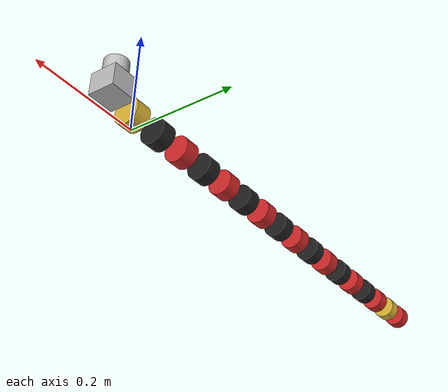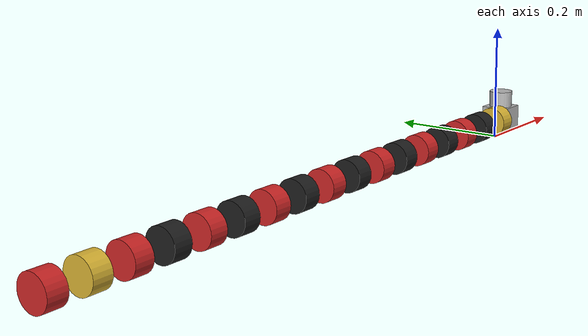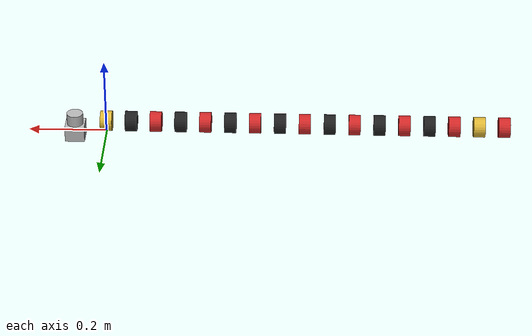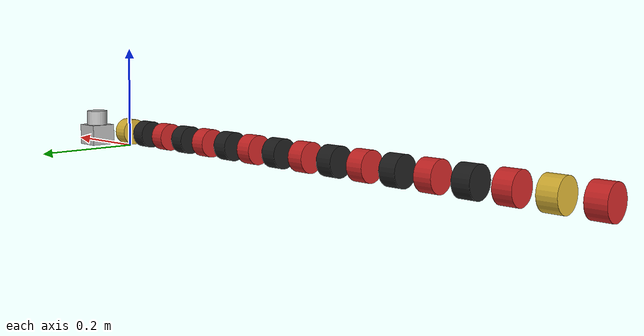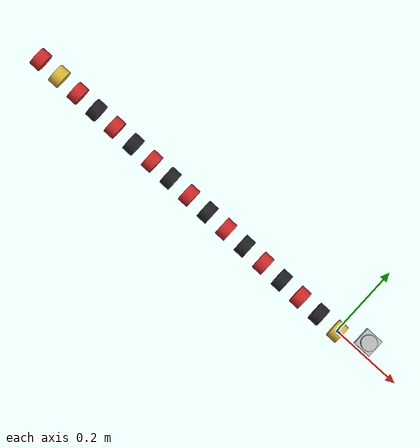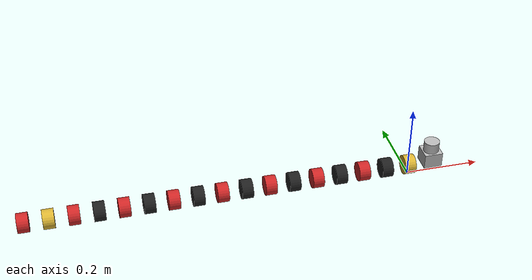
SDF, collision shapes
<?xml version='1.0'?>
<sdf version='1.6'>
  <model name='wl_snake'>
    <link name='module_1'>
      <pose frame=''>0 0 0.03 0 -0 0</pose>
      <inertial>
        <pose frame=''>0 0 0 0 -0 0</pose>
        <mass>0.1</mass>
        <inertia>
          <ixx>3.38e-05</ixx>
          <ixy>0</ixy>
          <ixz>0</ixz>
          <iyy>4.69e-05</iyy>
          <iyz>0</iyz>
          <izz>4.69e-05</izz>
        </inertia>
      </inertial>
      <self_collide>0</self_collide>
      <kinematic>0</kinematic>
      <sensor name='snake_camera' type='camera'>
        <pose frame=''>0.15 0 0 0 -0 0</pose>
        <update_rate>30</update_rate>
        <always_on>1</always_on>
        <visualize>1</visualize>
        <topic>/snake/eye</topic>
        <camera name='snake_eye'>
          <horizontal_fov>1.5708</horizontal_fov>
          <image>
            <width>320</width>
            <height>240</height>
            <format>R8G8B8</format>
          </image>
          <clip>
            <near>0.01</near>
            <far>100</far>
          </clip>
          <noise>
            <type>gaussian</type>
            <mean>0</mean>
            <stddev>0.007</stddev>
          </noise>
        </camera>
        <plugin name='camera_controller' filename='libgazebo_ros_camera.so'>
          <alwaysOn>true</alwaysOn>
          <updateRate>0.0</updateRate>
          <cameraName>snake/camera</cameraName>
          <imageTopicName>image_raw</imageTopicName>
          <cameraInfoTopicName>camera_info</cameraInfoTopicName>
          <frameName>camera_link</frameName>
          <hackBaseline>0.07</hackBaseline>
          <distortionK1>0.0</distortionK1>
          <distortionK2>0.0</distortionK2>
          <distortionK3>0.0</distortionK3>
          <distortionT1>0.0</distortionT1>
          <distortionT2>0.0</distortionT2>
          <robotNamespace>/</robotNamespace>
        </plugin>
      </sensor>
      <sensor name='dvs' type='camera'>
        <pose frame=''>0.15 0 0 0 -0 0</pose>
        <visualize>1</visualize>
        <camera name='__default__'>
          <horizontal_fov>1.5708</horizontal_fov>
          <image>
            <width>128</width>
            <height>128</height>
          </image>
          <clip>
            <near>0.01</near>
            <far>100</far>
          </clip>
        </camera>
        <always_on>1</always_on>
        <update_rate>60</update_rate>
        <visualize>0</visualize>
        <plugin name='dvs_controller' filename='libgazebo_dvs_plugin.so'>
          <cameraName>dvs128</cameraName>
          <robotNamespace>head</robotNamespace>
          <eventThreshold>10</eventThreshold>
          <cameraInfoTopicName>dvs_info</cameraInfoTopicName>
        </plugin>
        <pose frame=''>0 0 0 0 -0 0</pose>
      </sensor>
      <visual name='module_head_visual'>
        <pose frame=''>0.025 0 0 3.14159 -1.57079 3.14159</pose>
        <geometry>
          <cylinder>
            <radius>0.025</radius>
            <length>0.05</length>
          </cylinder>
        </geometry>
        <material>
          <script>
            <name>Gazebo/Gold</name>
            <uri>__default__</uri>
          </script>
          <specular>1 1 1 1</specular>
          <ambient>0.4 0.24869 0.020759 1</ambient>
          <diffuse>0.8 0.64869 0.120759 1</diffuse>
          <emissive>0 0 0 1</emissive>
        </material>
        <cast_shadows>1</cast_shadows>
        <transparency>0</transparency>
      </visual>
      <visual name='module_1_visual'>
        <pose frame=''>0 0 0 3.14159 -1.57079 3.14159</pose>
        <geometry>
          <cylinder>
            <radius>0.026</radius>
            <length>0.01</length>
          </cylinder>
        </geometry>
        <material>
          <script>
            <name>Gazebo/Red</name>
            <uri>__default__</uri>
          </script>
          <specular>1 1 1 1</specular>
          <ambient>1 0 0 1</ambient>
          <diffuse>1 0 0 1</diffuse>
          <emissive>0 0 0 1</emissive>
        </material>
        <cast_shadows>1</cast_shadows>
        <transparency>0</transparency>
      </visual>
      <visual name='module_1_visual_mesh_i'>
        <pose frame=''>-0.03 0 0 3.14159 -0 -1.5708</pose>
        <geometry>
          <mesh>
            <uri>/home/li/Downloads/wheel_less_snake/src/wl_snake_description/meshes/rotary_input.dae</uri>
            <scale>1 1 1</scale>
          </mesh>
        </geometry>
        <material>
          <script>
            <name>Gazebo/Gold</name>
            <uri>__default__</uri>
          </script>
          <specular>1 1 1 1</specular>
          <ambient>0.4 0.24869 0.020759 1</ambient>
          <diffuse>0.8 0.64869 0.120759 1</diffuse>
          <emissive>0 0 0 1</emissive>
        </material>
        <cast_shadows>1</cast_shadows>
        <transparency>0</transparency>
      </visual>
      <collision name='module_1_collision'>
        <laser_retro>0</laser_retro>
        <max_contacts>10</max_contacts>
        <pose frame=''>0 0 0 3.14159 -1.57079 3.14159</pose>
        <geometry>
          <cylinder>
            <radius>0.026</radius>
            <length>0.03</length>
          </cylinder>
        </geometry>
        <surface>
          <friction>
            <ode>
              <mu>1</mu>
              <mu2>1</mu2>
              <fdir1>0 0 0</fdir1>
              <slip1>0</slip1>
              <slip2>0</slip2>
            </ode>
            <torsional>
              <coefficient>1</coefficient>
              <patch_radius>0</patch_radius>
              <surface_radius>0</surface_radius>
              <use_patch_radius>1</use_patch_radius>
              <ode>
                <slip>0</slip>
              </ode>
            </torsional>
          </friction>
          <bounce>
            <restitution_coefficient>0</restitution_coefficient>
            <threshold>1e+06</threshold>
          </bounce>
          <contact>
            <collide_without_contact>0</collide_without_contact>
            <collide_without_contact_bitmask>1</collide_without_contact_bitmask>
            <collide_bitmask>1</collide_bitmask>
            <ode>
              <soft_cfm>0</soft_cfm>
              <soft_erp>0.2</soft_erp>
              <kp>1e+13</kp>
              <kd>1</kd>
              <max_vel>0.01</max_vel>
              <min_depth>0</min_depth>
            </ode>
            <bullet>
              <split_impulse>1</split_impulse>
              <split_impulse_penetration_threshold>-0.01</split_impulse_penetration_threshold>
              <soft_cfm>0</soft_cfm>
              <soft_erp>0.2</soft_erp>
              <kp>1e+13</kp>
              <kd>1</kd>
            </bullet>
          </contact>
        </surface>
      </collision>
    </link>
    <link name='module_10'>
      <pose frame=''>-0.576 0 0.03 0 -0 0</pose>
      <inertial>
        <pose frame=''>0 0 0 0 -0 0</pose>
        <mass>0.1</mass>
        <inertia>
          <ixx>3.38e-05</ixx>
          <ixy>0</ixy>
          <ixz>0</ixz>
          <iyy>4.69e-05</iyy>
          <iyz>0</iyz>
          <izz>4.69e-05</izz>
        </inertia>
      </inertial>
      <self_collide>0</self_collide>
      <kinematic>0</kinematic>
      <visual name='module_10_visual'>
        <pose frame=''>0 0 0 3.14159 -1.57079 3.14159</pose>
        <geometry>
          <cylinder>
            <radius>0.026</radius>
            <length>0.01</length>
          </cylinder>
        </geometry>
        <material>
          <script>
            <name>Gazebo/Black</name>
            <uri>__default__</uri>
          </script>
          <specular>1 1 1 1</specular>
          <ambient>0 0 0 1</ambient>
          <diffuse>0 0 0 1</diffuse>
          <emissive>0 0 0 1</emissive>
        </material>
        <cast_shadows>1</cast_shadows>
        <transparency>0</transparency>
      </visual>
      <visual name='module_10_visual_mesh_i'>
        <pose frame=''>-0.03 0 0 1.57079 1.57079 -3.14159</pose>
        <geometry>
          <mesh>
            <uri>/home/li/Downloads/wheel_less_snake/src/wl_snake_description/meshes/rotary_input.dae</uri>
            <scale>1 1 1</scale>
          </mesh>
        </geometry>
        <material>
          <script>
            <name>Gazebo/Gold</name>
            <uri>__default__</uri>
          </script>
          <specular>1 1 1 1</specular>
          <ambient>0.4 0.24869 0.020759 1</ambient>
          <diffuse>0.8 0.64869 0.120759 1</diffuse>
          <emissive>0 0 0 1</emissive>
        </material>
        <cast_shadows>1</cast_shadows>
        <transparency>0</transparency>
      </visual>
      <visual name='module_10_visual_mesh_o'>
        <pose frame=''>0.032 0 0 3.14159 -0 -1.5708</pose>
        <geometry>
          <mesh>
            <uri>/home/li/Downloads/wheel_less_snake/src/wl_snake_description/meshes/rotary_output.dae</uri>
            <scale>1 1 1</scale>
          </mesh>
        </geometry>
        <material>
          <script>
            <name>Gazebo/Gold</name>
            <uri>__default__</uri>
          </script>
          <specular>1 1 1 1</specular>
          <ambient>0.4 0.24869 0.020759 1</ambient>
          <diffuse>0.8 0.64869 0.120759 1</diffuse>
          <emissive>0 0 0 1</emissive>
        </material>
        <cast_shadows>1</cast_shadows>
        <transparency>0</transparency>
      </visual>
      <collision name='module_10_collision'>
        <laser_retro>0</laser_retro>
        <max_contacts>10</max_contacts>
        <pose frame=''>0 0 0 3.14159 -1.57079 3.14159</pose>
        <geometry>
          <cylinder>
            <radius>0.026</radius>
            <length>0.03</length>
          </cylinder>
        </geometry>
        <surface>
          <friction>
            <ode>
              <mu>1</mu>
              <mu2>1</mu2>
              <fdir1>0 0 0</fdir1>
              <slip1>0</slip1>
              <slip2>0</slip2>
            </ode>
            <torsional>
              <coefficient>1</coefficient>
              <patch_radius>0</patch_radius>
              <surface_radius>0</surface_radius>
              <use_patch_radius>1</use_patch_radius>
              <ode>
                <slip>0</slip>
              </ode>
            </torsional>
          </friction>
          <bounce>
            <restitution_coefficient>0</restitution_coefficient>
            <threshold>1e+06</threshold>
          </bounce>
          <contact>
            <collide_without_contact>0</collide_without_contact>
            <collide_without_contact_bitmask>1</collide_without_contact_bitmask>
            <collide_bitmask>1</collide_bitmask>
            <ode>
              <soft_cfm>0</soft_cfm>
              <soft_erp>0.2</soft_erp>
              <kp>1e+13</kp>
              <kd>1</kd>
              <max_vel>0.01</max_vel>
              <min_depth>0</min_depth>
            </ode>
            <bullet>
              <split_impulse>1</split_impulse>
              <split_impulse_penetration_threshold>-0.01</split_impulse_penetration_threshold>
              <soft_cfm>0</soft_cfm>
              <soft_erp>0.2</soft_erp>
              <kp>1e+13</kp>
              <kd>1</kd>
            </bullet>
          </contact>
        </surface>
      </collision>
    </link>
    <link name='module_11'>
      <pose frame=''>-0.64 0 0.03 0 -0 0</pose>
      <inertial>
        <pose frame=''>0 0 0 0 -0 0</pose>
        <mass>0.1</mass>
        <inertia>
          <ixx>3.38e-05</ixx>
          <ixy>0</ixy>
          <ixz>0</ixz>
          <iyy>4.69e-05</iyy>
          <iyz>0</iyz>
          <izz>4.69e-05</izz>
        </inertia>
      </inertial>
      <self_collide>0</self_collide>
      <kinematic>0</kinematic>
      <visual name='module_11_visual'>
        <pose frame=''>0 0 0 3.14159 -1.57079 3.14159</pose>
        <geometry>
          <cylinder>
            <radius>0.026</radius>
            <length>0.01</length>
          </cylinder>
        </geometry>
        <material>
          <script>
            <name>Gazebo/Red</name>
            <uri>__default__</uri>
          </script>
          <specular>1 1 1 1</specular>
          <ambient>1 0 0 1</ambient>
          <diffuse>1 0 0 1</diffuse>
          <emissive>0 0 0 1</emissive>
        </material>
        <cast_shadows>1</cast_shadows>
        <transparency>0</transparency>
      </visual>
      <visual name='module_11_visual_mesh_i'>
        <pose frame=''>-0.03 0 0 0 -0 1.5708</pose>
        <geometry>
          <mesh>
            <uri>/home/li/Downloads/wheel_less_snake/src/wl_snake_description/meshes/rotary_input.dae</uri>
            <scale>1 1 1</scale>
          </mesh>
        </geometry>
        <material>
          <script>
            <name>Gazebo/Gold</name>
            <uri>__default__</uri>
          </script>
          <specular>1 1 1 1</specular>
          <ambient>0.4 0.24869 0.020759 1</ambient>
          <diffuse>0.8 0.64869 0.120759 1</diffuse>
          <emissive>0 0 0 1</emissive>
        </material>
        <cast_shadows>1</cast_shadows>
        <transparency>0</transparency>
      </visual>
      <visual name='module_11_visual_mesh_o'>
        <pose frame=''>0.032 0 0 1.57079 1.57079 -3.14159</pose>
        <geometry>
          <mesh>
            <uri>/home/li/Downloads/wheel_less_snake/src/wl_snake_description/meshes/rotary_output.dae</uri>
            <scale>1 1 1</scale>
          </mesh>
        </geometry>
        <material>
          <script>
            <name>Gazebo/Gold</name>
            <uri>__default__</uri>
          </script>
          <specular>1 1 1 1</specular>
          <ambient>0.4 0.24869 0.020759 1</ambient>
          <diffuse>0.8 0.64869 0.120759 1</diffuse>
          <emissive>0 0 0 1</emissive>
        </material>
        <cast_shadows>1</cast_shadows>
        <transparency>0</transparency>
      </visual>
      <collision name='module_11_collision'>
        <laser_retro>0</laser_retro>
        <max_contacts>10</max_contacts>
        <pose frame=''>0 0 0 3.14159 -1.57079 3.14159</pose>
        <geometry>
          <cylinder>
            <radius>0.026</radius>
            <length>0.03</length>
          </cylinder>
        </geometry>
        <surface>
          <friction>
            <ode>
              <mu>1</mu>
              <mu2>1</mu2>
              <fdir1>0 0 0</fdir1>
              <slip1>0</slip1>
              <slip2>0</slip2>
            </ode>
            <torsional>
              <coefficient>1</coefficient>
              <patch_radius>0</patch_radius>
              <surface_radius>0</surface_radius>
              <use_patch_radius>1</use_patch_radius>
              <ode>
                <slip>0</slip>
              </ode>
            </torsional>
          </friction>
          <bounce>
            <restitution_coefficient>0</restitution_coefficient>
            <threshold>1e+06</threshold>
          </bounce>
          <contact>
            <collide_without_contact>0</collide_without_contact>
            <collide_without_contact_bitmask>1</collide_without_contact_bitmask>
            <collide_bitmask>1</collide_bitmask>
            <ode>
              <soft_cfm>0</soft_cfm>
              <soft_erp>0.2</soft_erp>
              <kp>1e+13</kp>
              <kd>1</kd>
              <max_vel>0.01</max_vel>
              <min_depth>0</min_depth>
            </ode>
            <bullet>
              <split_impulse>1</split_impulse>
              <split_impulse_penetration_threshold>-0.01</split_impulse_penetration_threshold>
              <soft_cfm>0</soft_cfm>
              <soft_erp>0.2</soft_erp>
              <kp>1e+13</kp>
              <kd>1</kd>
            </bullet>
          </contact>
        </surface>
      </collision>
    </link>
    <link name='module_12'>
      <pose frame=''>-0.704 0 0.03 0 -0 0</pose>
      <inertial>
        <pose frame=''>0 0 0 0 -0 0</pose>
        <mass>0.1</mass>
        <inertia>
          <ixx>3.38e-05</ixx>
          <ixy>0</ixy>
          <ixz>0</ixz>
          <iyy>4.69e-05</iyy>
          <iyz>0</iyz>
          <izz>4.69e-05</izz>
        </inertia>
      </inertial>
      <self_collide>0</self_collide>
      <kinematic>0</kinematic>
      <visual name='module_12_visual'>
        <pose frame=''>0 0 0 3.14159 -1.57079 3.14159</pose>
        <geometry>
          <cylinder>
            <radius>0.026</radius>
            <length>0.01</length>
          </cylinder>
        </geometry>
        <material>
          <script>
            <name>Gazebo/Black</name>
            <uri>__default__</uri>
          </script>
          <specular>1 1 1 1</specular>
          <ambient>0 0 0 1</ambient>
          <diffuse>0 0 0 1</diffuse>
          <emissive>0 0 0 1</emissive>
        </material>
        <cast_shadows>1</cast_shadows>
        <transparency>0</transparency>
      </visual>
      <visual name='module_12_visual_mesh_i'>
        <pose frame=''>-0.03 0 0 -1.57079 -1.57079 -3.14159</pose>
        <geometry>
          <mesh>
            <uri>/home/li/Downloads/wheel_less_snake/src/wl_snake_description/meshes/rotary_input.dae</uri>
            <scale>1 1 1</scale>
          </mesh>
        </geometry>
        <material>
          <script>
            <name>Gazebo/Gold</name>
            <uri>__default__</uri>
          </script>
          <specular>1 1 1 1</specular>
          <ambient>0.4 0.24869 0.020759 1</ambient>
          <diffuse>0.8 0.64869 0.120759 1</diffuse>
          <emissive>0 0 0 1</emissive>
        </material>
        <cast_shadows>1</cast_shadows>
        <transparency>0</transparency>
      </visual>
      <visual name='module_12_visual_mesh_o'>
        <pose frame=''>0.032 0 0 0 -0 1.5708</pose>
        <geometry>
          <mesh>
            <uri>/home/li/Downloads/wheel_less_snake/src/wl_snake_description/meshes/rotary_output.dae</uri>
            <scale>1 1 1</scale>
          </mesh>
        </geometry>
        <material>
          <script>
            <name>Gazebo/Gold</name>
            <uri>__default__</uri>
          </script>
          <specular>1 1 1 1</specular>
          <ambient>0.4 0.24869 0.020759 1</ambient>
          <diffuse>0.8 0.64869 0.120759 1</diffuse>
          <emissive>0 0 0 1</emissive>
        </material>
        <cast_shadows>1</cast_shadows>
        <transparency>0</transparency>
      </visual>
      <collision name='module_12_collision'>
        <laser_retro>0</laser_retro>
        <max_contacts>10</max_contacts>
        <pose frame=''>0 0 0 3.14159 -1.57079 3.14159</pose>
        <geometry>
          <cylinder>
            <radius>0.026</radius>
            <length>0.03</length>
          </cylinder>
        </geometry>
        <surface>
          <friction>
            <ode>
              <mu>1</mu>
              <mu2>1</mu2>
              <fdir1>0 0 0</fdir1>
              <slip1>0</slip1>
              <slip2>0</slip2>
            </ode>
            <torsional>
              <coefficient>1</coefficient>
              <patch_radius>0</patch_radius>
              <surface_radius>0</surface_radius>
              <use_patch_radius>1</use_patch_radius>
              <ode>
                <slip>0</slip>
              </ode>
            </torsional>
          </friction>
          <bounce>
            <restitution_coefficient>0</restitution_coefficient>
            <threshold>1e+06</threshold>
          </bounce>
          <contact>
            <collide_without_contact>0</collide_without_contact>
            <collide_without_contact_bitmask>1</collide_without_contact_bitmask>
            <collide_bitmask>1</collide_bitmask>
            <ode>
              <soft_cfm>0</soft_cfm>
              <soft_erp>0.2</soft_erp>
              <kp>1e+13</kp>
              <kd>1</kd>
              <max_vel>0.01</max_vel>
              <min_depth>0</min_depth>
            </ode>
            <bullet>
              <split_impulse>1</split_impulse>
              <split_impulse_penetration_threshold>-0.01</split_impulse_penetration_threshold>
              <soft_cfm>0</soft_cfm>
              <soft_erp>0.2</soft_erp>
              <kp>1e+13</kp>
              <kd>1</kd>
            </bullet>
          </contact>
        </surface>
      </collision>
    </link>
    <link name='module_13'>
      <pose frame=''>-0.768 0 0.03 0 -0 0</pose>
      <inertial>
        <pose frame=''>0 0 0 0 -0 0</pose>
        <mass>0.1</mass>
        <inertia>
          <ixx>3.38e-05</ixx>
          <ixy>0</ixy>
          <ixz>0</ixz>
          <iyy>4.69e-05</iyy>
          <iyz>0</iyz>
          <izz>4.69e-05</izz>
        </inertia>
      </inertial>
      <self_collide>0</self_collide>
      <kinematic>0</kinematic>
      <visual name='module_13_visual'>
        <pose frame=''>0 0 0 3.14159 -1.57079 3.14159</pose>
        <geometry>
          <cylinder>
            <radius>0.026</radius>
            <length>0.01</length>
          </cylinder>
        </geometry>
        <material>
          <script>
            <name>Gazebo/Red</name>
            <uri>__default__</uri>
          </script>
          <specular>1 1 1 1</specular>
          <ambient>1 0 0 1</ambient>
          <diffuse>1 0 0 1</diffuse>
          <emissive>0 0 0 1</emissive>
        </material>
        <cast_shadows>1</cast_shadows>
        <transparency>0</transparency>
      </visual>
      <visual name='module_13_visual_mesh_i'>
        <pose frame=''>-0.03 0 0 3.14159 -0 -1.5708</pose>
        <geometry>
          <mesh>
            <uri>/home/li/Downloads/wheel_less_snake/src/wl_snake_description/meshes/rotary_input.dae</uri>
            <scale>1 1 1</scale>
          </mesh>
        </geometry>
        <material>
          <script>
            <name>Gazebo/Gold</name>
            <uri>__default__</uri>
          </script>
          <specular>1 1 1 1</specular>
          <ambient>0.4 0.24869 0.020759 1</ambient>
          <diffuse>0.8 0.64869 0.120759 1</diffuse>
          <emissive>0 0 0 1</emissive>
        </material>
        <cast_shadows>1</cast_shadows>
        <transparency>0</transparency>
      </visual>
      <visual name='module_13_visual_mesh_o'>
        <pose frame=''>0.032 0 0 -1.57079 -1.57079 -3.14159</pose>
        <geometry>
          <mesh>
            <uri>/home/li/Downloads/wheel_less_snake/src/wl_snake_description/meshes/rotary_output.dae</uri>
            <scale>1 1 1</scale>
          </mesh>
        </geometry>
        <material>
          <script>
            <name>Gazebo/Gold</name>
            <uri>__default__</uri>
          </script>
          <specular>1 1 1 1</specular>
          <ambient>0.4 0.24869 0.020759 1</ambient>
          <diffuse>0.8 0.64869 0.120759 1</diffuse>
          <emissive>0 0 0 1</emissive>
        </material>
        <cast_shadows>1</cast_shadows>
        <transparency>0</transparency>
      </visual>
      <collision name='module_13_collision'>
        <laser_retro>0</laser_retro>
        <max_contacts>10</max_contacts>
        <pose frame=''>0 0 0 3.14159 -1.57079 3.14159</pose>
        <geometry>
          <cylinder>
            <radius>0.026</radius>
            <length>0.03</length>
          </cylinder>
        </geometry>
        <surface>
          <friction>
            <ode>
              <mu>1</mu>
              <mu2>1</mu2>
              <fdir1>0 0 0</fdir1>
              <slip1>0</slip1>
              <slip2>0</slip2>
            </ode>
            <torsional>
              <coefficient>1</coefficient>
              <patch_radius>0</patch_radius>
              <surface_radius>0</surface_radius>
              <use_patch_radius>1</use_patch_radius>
              <ode>
                <slip>0</slip>
              </ode>
            </torsional>
          </friction>
          <bounce>
            <restitution_coefficient>0</restitution_coefficient>
            <threshold>1e+06</threshold>
          </bounce>
          <contact>
            <collide_without_contact>0</collide_without_contact>
            <collide_without_contact_bitmask>1</collide_without_contact_bitmask>
            <collide_bitmask>1</collide_bitmask>
            <ode>
              <soft_cfm>0</soft_cfm>
              <soft_erp>0.2</soft_erp>
              <kp>1e+13</kp>
              <kd>1</kd>
              <max_vel>0.01</max_vel>
              <min_depth>0</min_depth>
            </ode>
            <bullet>
              <split_impulse>1</split_impulse>
              <split_impulse_penetration_threshold>-0.01</split_impulse_penetration_threshold>
              <soft_cfm>0</soft_cfm>
              <soft_erp>0.2</soft_erp>
              <kp>1e+13</kp>
              <kd>1</kd>
            </bullet>
          </contact>
        </surface>
      </collision>
    </link>
    <link name='module_14'>
      <pose frame=''>-0.832 0 0.03 0 -0 0</pose>
      <inertial>
        <pose frame=''>0 0 0 0 -0 0</pose>
        <mass>0.1</mass>
        <inertia>
          <ixx>3.38e-05</ixx>
          <ixy>0</ixy>
          <ixz>0</ixz>
          <iyy>4.69e-05</iyy>
          <iyz>0</iyz>
          <izz>4.69e-05</izz>
        </inertia>
      </inertial>
      <self_collide>0</self_collide>
      <kinematic>0</kinematic>
      <visual name='module_14_visual'>
        <pose frame=''>0 0 0 3.14159 -1.57079 3.14159</pose>
        <geometry>
          <cylinder>
            <radius>0.026</radius>
            <length>0.01</length>
          </cylinder>
        </geometry>
        <material>
          <script>
            <name>Gazebo/Black</name>
            <uri>__default__</uri>
          </script>
          <specular>1 1 1 1</specular>
          <ambient>0 0 0 1</ambient>
          <diffuse>0 0 0 1</diffuse>
          <emissive>0 0 0 1</emissive>
        </material>
        <cast_shadows>1</cast_shadows>
        <transparency>0</transparency>
      </visual>
      <visual name='module_14_visual_mesh_i'>
        <pose frame=''>-0.03 0 0 1.57079 1.57079 -3.14159</pose>
        <geometry>
          <mesh>
            <uri>/home/li/Downloads/wheel_less_snake/src/wl_snake_description/meshes/rotary_input.dae</uri>
            <scale>1 1 1</scale>
          </mesh>
        </geometry>
        <material>
          <script>
            <name>Gazebo/Gold</name>
            <uri>__default__</uri>
          </script>
          <specular>1 1 1 1</specular>
          <ambient>0.4 0.24869 0.020759 1</ambient>
          <diffuse>0.8 0.64869 0.120759 1</diffuse>
          <emissive>0 0 0 1</emissive>
        </material>
        <cast_shadows>1</cast_shadows>
        <transparency>0</transparency>
      </visual>
      <visual name='module_14_visual_mesh_o'>
        <pose frame=''>0.032 0 0 3.14159 -0 -1.5708</pose>
        <geometry>
          <mesh>
            <uri>/home/li/Downloads/wheel_less_snake/src/wl_snake_description/meshes/rotary_output.dae</uri>
            <scale>1 1 1</scale>
          </mesh>
        </geometry>
        <material>
          <script>
            <name>Gazebo/Gold</name>
            <uri>__default__</uri>
          </script>
          <specular>1 1 1 1</specular>
          <ambient>0.4 0.24869 0.020759 1</ambient>
          <diffuse>0.8 0.64869 0.120759 1</diffuse>
          <emissive>0 0 0 1</emissive>
        </material>
        <cast_shadows>1</cast_shadows>
        <transparency>0</transparency>
      </visual>
      <collision name='module_14_collision'>
        <laser_retro>0</laser_retro>
        <max_contacts>10</max_contacts>
        <pose frame=''>0 0 0 3.14159 -1.57079 3.14159</pose>
        <geometry>
          <cylinder>
            <radius>0.026</radius>
            <length>0.03</length>
          </cylinder>
        </geometry>
        <surface>
          <friction>
            <ode>
              <mu>1</mu>
              <mu2>1</mu2>
              <fdir1>0 0 0</fdir1>
              <slip1>0</slip1>
              <slip2>0</slip2>
            </ode>
            <torsional>
              <coefficient>1</coefficient>
              <patch_radius>0</patch_radius>
              <surface_radius>0</surface_radius>
              <use_patch_radius>1</use_patch_radius>
              <ode>
                <slip>0</slip>
              </ode>
            </torsional>
          </friction>
          <bounce>
            <restitution_coefficient>0</restitution_coefficient>
            <threshold>1e+06</threshold>
          </bounce>
          <contact>
            <collide_without_contact>0</collide_without_contact>
            <collide_without_contact_bitmask>1</collide_without_contact_bitmask>
            <collide_bitmask>1</collide_bitmask>
            <ode>
              <soft_cfm>0</soft_cfm>
              <soft_erp>0.2</soft_erp>
              <kp>1e+13</kp>
              <kd>1</kd>
              <max_vel>0.01</max_vel>
              <min_depth>0</min_depth>
            </ode>
            <bullet>
              <split_impulse>1</split_impulse>
              <split_impulse_penetration_threshold>-0.01</split_impulse_penetration_threshold>
              <soft_cfm>0</soft_cfm>
              <soft_erp>0.2</soft_erp>
              <kp>1e+13</kp>
              <kd>1</kd>
            </bullet>
          </contact>
        </surface>
      </collision>
    </link>
    <link name='module_15'>
      <pose frame=''>-0.896 0 0.03 0 -0 0</pose>
      <inertial>
        <pose frame=''>0 0 0 0 -0 0</pose>
        <mass>0.1</mass>
        <inertia>
          <ixx>3.38e-05</ixx>
          <ixy>0</ixy>
          <ixz>0</ixz>
          <iyy>4.69e-05</iyy>
          <iyz>0</iyz>
          <izz>4.69e-05</izz>
        </inertia>
      </inertial>
      <self_collide>0</self_collide>
      <kinematic>0</kinematic>
      <visual name='module_15_visual'>
        <pose frame=''>0 0 0 3.14159 -1.57079 3.14159</pose>
        <geometry>
          <cylinder>
            <radius>0.026</radius>
            <length>0.01</length>
          </cylinder>
        </geometry>
        <material>
          <script>
            <name>Gazebo/Red</name>
            <uri>__default__</uri>
          </script>
          <specular>1 1 1 1</specular>
          <ambient>1 0 0 1</ambient>
          <diffuse>1 0 0 1</diffuse>
          <emissive>0 0 0 1</emissive>
        </material>
        <cast_shadows>1</cast_shadows>
        <transparency>0</transparency>
      </visual>
      <visual name='module_15_visual_mesh_i'>
        <pose frame=''>-0.03 0 0 0 -0 1.5708</pose>
        <geometry>
          <mesh>
            <uri>/home/li/Downloads/wheel_less_snake/src/wl_snake_description/meshes/rotary_input.dae</uri>
            <scale>1 1 1</scale>
          </mesh>
        </geometry>
        <material>
          <script>
            <name>Gazebo/Gold</name>
            <uri>__default__</uri>
          </script>
          <specular>1 1 1 1</specular>
          <ambient>0.4 0.24869 0.020759 1</ambient>
          <diffuse>0.8 0.64869 0.120759 1</diffuse>
          <emissive>0 0 0 1</emissive>
        </material>
        <cast_shadows>1</cast_shadows>
        <transparency>0</transparency>
      </visual>
      <visual name='module_15_visual_mesh_o'>
        <pose frame=''>0.032 0 0 1.57079 1.57079 -3.14159</pose>
        <geometry>
          <mesh>
            <uri>/home/li/Downloads/wheel_less_snake/src/wl_snake_description/meshes/rotary_output.dae</uri>
            <scale>1 1 1</scale>
          </mesh>
        </geometry>
        <material>
          <script>
            <name>Gazebo/Gold</name>
            <uri>__default__</uri>
          </script>
          <specular>1 1 1 1</specular>
          <ambient>0.4 0.24869 0.020759 1</ambient>
          <diffuse>0.8 0.64869 0.120759 1</diffuse>
          <emissive>0 0 0 1</emissive>
        </material>
        <cast_shadows>1</cast_shadows>
        <transparency>0</transparency>
      </visual>
      <collision name='module_15_collision'>
        <laser_retro>0</laser_retro>
        <max_contacts>10</max_contacts>
        <pose frame=''>0 0 0 3.14159 -1.57079 3.14159</pose>
        <geometry>
          <cylinder>
            <radius>0.026</radius>
            <length>0.03</length>
          </cylinder>
        </geometry>
        <surface>
          <friction>
            <ode>
              <mu>1</mu>
              <mu2>1</mu2>
              <fdir1>0 0 0</fdir1>
              <slip1>0</slip1>
              <slip2>0</slip2>
            </ode>
            <torsional>
              <coefficient>1</coefficient>
              <patch_radius>0</patch_radius>
              <surface_radius>0</surface_radius>
              <use_patch_radius>1</use_patch_radius>
              <ode>
                <slip>0</slip>
              </ode>
            </torsional>
          </friction>
          <bounce>
            <restitution_coefficient>0</restitution_coefficient>
            <threshold>1e+06</threshold>
          </bounce>
          <contact>
            <collide_without_contact>0</collide_without_contact>
            <collide_without_contact_bitmask>1</collide_without_contact_bitmask>
            <collide_bitmask>1</collide_bitmask>
            <ode>
              <soft_cfm>0</soft_cfm>
              <soft_erp>0.2</soft_erp>
              <kp>1e+13</kp>
              <kd>1</kd>
              <max_vel>0.01</max_vel>
              <min_depth>0</min_depth>
            </ode>
            <bullet>
              <split_impulse>1</split_impulse>
              <split_impulse_penetration_threshold>-0.01</split_impulse_penetration_threshold>
              <soft_cfm>0</soft_cfm>
              <soft_erp>0.2</soft_erp>
              <kp>1e+13</kp>
              <kd>1</kd>
            </bullet>
          </contact>
        </surface>
      </collision>
    </link>
    <link name='module_16'>
      <pose frame=''>-0.96 0 0.03 0 -0 0</pose>
      <inertial>
        <pose frame=''>0 0 0 0 -0 0</pose>
        <mass>0.1</mass>
        <inertia>
          <ixx>3.38e-05</ixx>
          <ixy>0</ixy>
          <ixz>0</ixz>
          <iyy>4.69e-05</iyy>
          <iyz>0</iyz>
          <izz>4.69e-05</izz>
        </inertia>
      </inertial>
      <self_collide>0</self_collide>
      <kinematic>0</kinematic>
      <visual name='module_16_visual_mesh_i'>
        <pose frame=''>-0.03 0 0 -1.57079 -1.57079 -3.14159</pose>
        <geometry>
          <mesh>
            <uri>/home/li/Downloads/wheel_less_snake/src/wl_snake_description/meshes/rotary_input.dae</uri>
            <scale>1 1 1</scale>
          </mesh>
        </geometry>
        <material>
          <script>
            <name>Gazebo/Gold</name>
            <uri>__default__</uri>
          </script>
          <specular>1 1 1 1</specular>
          <ambient>0.4 0.24869 0.020759 1</ambient>
          <diffuse>0.8 0.64869 0.120759 1</diffuse>
          <emissive>0 0 0 1</emissive>
        </material>
        <cast_shadows>1</cast_shadows>
        <transparency>0</transparency>
      </visual>
      <visual name='module_16_visual'>
        <pose frame=''>0 0 0 3.14159 -1.57079 3.14159</pose>
        <geometry>
          <cylinder>
            <radius>0.026</radius>
            <length>0.01</length>
          </cylinder>
        </geometry>
        <material>
          <script>
            <name>Gazebo/Black</name>
            <uri>__default__</uri>
          </script>
          <specular>1 1 1 1</specular>
          <ambient>0 0 0 1</ambient>
          <diffuse>0 0 0 1</diffuse>
          <emissive>0 0 0 1</emissive>
        </material>
        <cast_shadows>1</cast_shadows>
        <transparency>0</transparency>
      </visual>
      <visual name='module_16_visual_mesh_o'>
        <pose frame=''>0.032 0 0 0 -0 1.5708</pose>
        <geometry>
          <mesh>
            <uri>/home/li/Downloads/wheel_less_snake/src/wl_snake_description/meshes/rotary_output.dae</uri>
            <scale>1 1 1</scale>
          </mesh>
        </geometry>
        <material>
          <script>
            <name>Gazebo/Gold</name>
            <uri>__default__</uri>
          </script>
          <specular>1 1 1 1</specular>
          <ambient>0.4 0.24869 0.020759 1</ambient>
          <diffuse>0.8 0.64869 0.120759 1</diffuse>
          <emissive>0 0 0 1</emissive>
        </material>
        <cast_shadows>1</cast_shadows>
        <transparency>0</transparency>
      </visual>
      <collision name='module_16_collision'>
        <laser_retro>0</laser_retro>
        <max_contacts>10</max_contacts>
        <pose frame=''>0 0 0 3.14159 -1.57079 3.14159</pose>
        <geometry>
          <cylinder>
            <radius>0.026</radius>
            <length>0.03</length>
          </cylinder>
        </geometry>
        <surface>
          <friction>
            <ode>
              <mu>1</mu>
              <mu2>1</mu2>
              <fdir1>0 0 0</fdir1>
              <slip1>0</slip1>
              <slip2>0</slip2>
            </ode>
            <torsional>
              <coefficient>1</coefficient>
              <patch_radius>0</patch_radius>
              <surface_radius>0</surface_radius>
              <use_patch_radius>1</use_patch_radius>
              <ode>
                <slip>0</slip>
              </ode>
            </torsional>
          </friction>
          <bounce>
            <restitution_coefficient>0</restitution_coefficient>
            <threshold>1e+06</threshold>
          </bounce>
          <contact>
            <collide_without_contact>0</collide_without_contact>
            <collide_without_contact_bitmask>1</collide_without_contact_bitmask>
            <collide_bitmask>1</collide_bitmask>
            <ode>
              <soft_cfm>0</soft_cfm>
              <soft_erp>0.2</soft_erp>
              <kp>1e+13</kp>
              <kd>1</kd>
              <max_vel>0.01</max_vel>
              <min_depth>0</min_depth>
            </ode>
            <bullet>
              <split_impulse>1</split_impulse>
              <split_impulse_penetration_threshold>-0.01</split_impulse_penetration_threshold>
              <soft_cfm>0</soft_cfm>
              <soft_erp>0.2</soft_erp>
              <kp>1e+13</kp>
              <kd>1</kd>
            </bullet>
          </contact>
        </surface>
      </collision>
    </link>
    <link name='module_17'>
      <pose frame=''>-1.024 0 0.03 0 -0 0</pose>
      <inertial>
        <pose frame=''>0 0 0 0 -0 0</pose>
        <mass>0.1</mass>
        <inertia>
          <ixx>3.38e-05</ixx>
          <ixy>0</ixy>
          <ixz>0</ixz>
          <iyy>4.69e-05</iyy>
          <iyz>0</iyz>
          <izz>4.69e-05</izz>
        </inertia>
      </inertial>
      <self_collide>0</self_collide>
      <kinematic>0</kinematic>
      <visual name='module_17_visual'>
        <pose frame=''>0 0 0 3.14159 -1.57079 3.14159</pose>
        <geometry>
          <cylinder>
            <radius>0.026</radius>
            <length>0.01</length>
          </cylinder>
        </geometry>
        <material>
          <script>
            <name>Gazebo/Red</name>
            <uri>__default__</uri>
          </script>
          <specular>1 1 1 1</specular>
          <ambient>1 0 0 1</ambient>
          <diffuse>1 0 0 1</diffuse>
          <emissive>0 0 0 1</emissive>
        </material>
        <cast_shadows>1</cast_shadows>
        <transparency>0</transparency>
      </visual>
      <visual name='module_17_visual_mesh_i'>
        <pose frame=''>-0.03 0 0 3.14159 -0 -1.5708</pose>
        <geometry>
          <mesh>
            <uri>/home/li/Downloads/wheel_less_snake/src/wl_snake_description/meshes/rotary_input.dae</uri>
            <scale>1 1 1</scale>
          </mesh>
        </geometry>
        <material>
          <script>
            <name>Gazebo/Gold</name>
            <uri>__default__</uri>
          </script>
          <specular>1 1 1 1</specular>
          <ambient>0.4 0.24869 0.020759 1</ambient>
          <diffuse>0.8 0.64869 0.120759 1</diffuse>
          <emissive>0 0 0 1</emissive>
        </material>
        <cast_shadows>1</cast_shadows>
        <transparency>0</transparency>
      </visual>
      <visual name='module_17_visual_mesh_o'>
        <pose frame=''>0.032 0 0 -1.57079 -1.57079 -3.14159</pose>
        <geometry>
          <mesh>
            <uri>/home/li/Downloads/wheel_less_snake/src/wl_snake_description/meshes/rotary_output.dae</uri>
            <scale>1 1 1</scale>
          </mesh>
        </geometry>
        <material>
          <script>
            <name>Gazebo/Gold</name>
            <uri>__default__</uri>
          </script>
          <specular>1 1 1 1</specular>
          <ambient>0.4 0.24869 0.020759 1</ambient>
          <diffuse>0.8 0.64869 0.120759 1</diffuse>
          <emissive>0 0 0 1</emissive>
        </material>
        <cast_shadows>1</cast_shadows>
        <transparency>0</transparency>
      </visual>
      <collision name='module_17_collision'>
        <laser_retro>0</laser_retro>
        <max_contacts>10</max_contacts>
        <pose frame=''>0 0 0 3.14159 -1.57079 3.14159</pose>
        <geometry>
          <cylinder>
            <radius>0.026</radius>
            <length>0.03</length>
          </cylinder>
        </geometry>
        <surface>
          <friction>
            <ode>
              <mu>1</mu>
              <mu2>1</mu2>
              <fdir1>0 0 0</fdir1>
              <slip1>0</slip1>
              <slip2>0</slip2>
            </ode>
            <torsional>
              <coefficient>1</coefficient>
              <patch_radius>0</patch_radius>
              <surface_radius>0</surface_radius>
              <use_patch_radius>1</use_patch_radius>
              <ode>
                <slip>0</slip>
              </ode>
            </torsional>
          </friction>
          <bounce>
            <restitution_coefficient>0</restitution_coefficient>
            <threshold>1e+06</threshold>
          </bounce>
          <contact>
            <collide_without_contact>0</collide_without_contact>
            <collide_without_contact_bitmask>1</collide_without_contact_bitmask>
            <collide_bitmask>1</collide_bitmask>
            <ode>
              <soft_cfm>0</soft_cfm>
              <soft_erp>0.2</soft_erp>
              <kp>1e+13</kp>
              <kd>1</kd>
              <max_vel>0.01</max_vel>
              <min_depth>0</min_depth>
            </ode>
            <bullet>
              <split_impulse>1</split_impulse>
              <split_impulse_penetration_threshold>-0.01</split_impulse_penetration_threshold>
              <soft_cfm>0</soft_cfm>
              <soft_erp>0.2</soft_erp>
              <kp>1e+13</kp>
              <kd>1</kd>
            </bullet>
          </contact>
        </surface>
      </collision>
    </link>
    <link name='module_2'>
      <pose frame=''>-0.064 0 0.03 0 -0 0</pose>
      <inertial>
        <pose frame=''>0 0 0 0 -0 0</pose>
        <mass>0.1</mass>
        <inertia>
          <ixx>3.38e-05</ixx>
          <ixy>0</ixy>
          <ixz>0</ixz>
          <iyy>4.69e-05</iyy>
          <iyz>0</iyz>
          <izz>4.69e-05</izz>
        </inertia>
      </inertial>
      <self_collide>0</self_collide>
      <kinematic>0</kinematic>
      <visual name='module_2_visual'>
        <pose frame=''>0 0 0 3.14159 -1.57079 3.14159</pose>
        <geometry>
          <cylinder>
            <radius>0.026</radius>
            <length>0.01</length>
          </cylinder>
        </geometry>
        <material>
          <script>
            <name>Gazebo/Black</name>
            <uri>__default__</uri>
          </script>
          <specular>1 1 1 1</specular>
          <ambient>0 0 0 1</ambient>
          <diffuse>0 0 0 1</diffuse>
          <emissive>0 0 0 1</emissive>
        </material>
        <cast_shadows>1</cast_shadows>
        <transparency>0</transparency>
      </visual>
      <visual name='module_2_visual_mesh_o'>
        <pose frame=''>0.032 0 0 3.14159 -0 -1.5708</pose>
        <geometry>
          <mesh>
            <uri>/home/li/Downloads/wheel_less_snake/src/wl_snake_description/meshes/rotary_output.dae</uri>
            <scale>1 1 1</scale>
          </mesh>
        </geometry>
        <material>
          <script>
            <name>Gazebo/Gold</name>
            <uri>__default__</uri>
          </script>
          <specular>1 1 1 1</specular>
          <ambient>0.4 0.24869 0.020759 1</ambient>
          <diffuse>0.8 0.64869 0.120759 1</diffuse>
          <emissive>0 0 0 1</emissive>
        </material>
        <cast_shadows>1</cast_shadows>
        <transparency>0</transparency>
      </visual>
      <visual name='module_2_visual_mesh_i'>
        <pose frame=''>-0.03 0 0 1.57079 1.57079 -3.14159</pose>
        <geometry>
          <mesh>
            <uri>/home/li/Downloads/wheel_less_snake/src/wl_snake_description/meshes/rotary_input.dae</uri>
            <scale>1 1 1</scale>
          </mesh>
        </geometry>
        <material>
          <script>
            <name>Gazebo/Gold</name>
            <uri>__default__</uri>
          </script>
          <specular>1 1 1 1</specular>
          <ambient>0.4 0.24869 0.020759 1</ambient>
          <diffuse>0.8 0.64869 0.120759 1</diffuse>
          <emissive>0 0 0 1</emissive>
        </material>
        <cast_shadows>1</cast_shadows>
        <transparency>0</transparency>
      </visual>
      <collision name='module_2_collision'>
        <laser_retro>0</laser_retro>
        <max_contacts>10</max_contacts>
        <pose frame=''>0 0 0 3.14159 -1.57079 3.14159</pose>
        <geometry>
          <cylinder>
            <radius>0.026</radius>
            <length>0.03</length>
          </cylinder>
        </geometry>
        <surface>
          <friction>
            <ode>
              <mu>1</mu>
              <mu2>1</mu2>
              <fdir1>0 0 0</fdir1>
              <slip1>0</slip1>
              <slip2>0</slip2>
            </ode>
            <torsional>
              <coefficient>1</coefficient>
              <patch_radius>0</patch_radius>
              <surface_radius>0</surface_radius>
              <use_patch_radius>1</use_patch_radius>
              <ode>
                <slip>0</slip>
              </ode>
            </torsional>
          </friction>
          <bounce>
            <restitution_coefficient>0</restitution_coefficient>
            <threshold>1e+06</threshold>
          </bounce>
          <contact>
            <collide_without_contact>0</collide_without_contact>
            <collide_without_contact_bitmask>1</collide_without_contact_bitmask>
            <collide_bitmask>1</collide_bitmask>
            <ode>
              <soft_cfm>0</soft_cfm>
              <soft_erp>0.2</soft_erp>
              <kp>1e+13</kp>
              <kd>1</kd>
              <max_vel>0.01</max_vel>
              <min_depth>0</min_depth>
            </ode>
            <bullet>
              <split_impulse>1</split_impulse>
              <split_impulse_penetration_threshold>-0.01</split_impulse_penetration_threshold>
              <soft_cfm>0</soft_cfm>
              <soft_erp>0.2</soft_erp>
              <kp>1e+13</kp>
              <kd>1</kd>
            </bullet>
          </contact>
        </surface>
      </collision>
    </link>
    <link name='module_3'>
      <pose frame=''>-0.128 0 0.03 0 -0 0</pose>
      <inertial>
        <pose frame=''>0 0 0 0 -0 0</pose>
        <mass>0.1</mass>
        <inertia>
          <ixx>3.38e-05</ixx>
          <ixy>0</ixy>
          <ixz>0</ixz>
          <iyy>4.69e-05</iyy>
          <iyz>0</iyz>
          <izz>4.69e-05</izz>
        </inertia>
      </inertial>
      <self_collide>0</self_collide>
      <kinematic>0</kinematic>
      <visual name='module_3_visual'>
        <pose frame=''>0 0 0 3.14159 -1.57079 3.14159</pose>
        <geometry>
          <cylinder>
            <radius>0.026</radius>
            <length>0.01</length>
          </cylinder>
        </geometry>
        <material>
          <script>
            <name>Gazebo/Red</name>
            <uri>__default__</uri>
          </script>
          <specular>1 1 1 1</specular>
          <ambient>1 0 0 1</ambient>
          <diffuse>1 0 0 1</diffuse>
          <emissive>0 0 0 1</emissive>
        </material>
        <cast_shadows>1</cast_shadows>
        <transparency>0</transparency>
      </visual>
      <visual name='module_3_visual_mesh_i'>
        <pose frame=''>-0.03 0 0 0 -0 1.5708</pose>
        <geometry>
          <mesh>
            <uri>/home/li/Downloads/wheel_less_snake/src/wl_snake_description/meshes/rotary_input.dae</uri>
            <scale>1 1 1</scale>
          </mesh>
        </geometry>
        <material>
          <script>
            <name>Gazebo/Gold</name>
            <uri>__default__</uri>
          </script>
          <specular>1 1 1 1</specular>
          <ambient>0.4 0.24869 0.020759 1</ambient>
          <diffuse>0.8 0.64869 0.120759 1</diffuse>
          <emissive>0 0 0 1</emissive>
        </material>
        <cast_shadows>1</cast_shadows>
        <transparency>0</transparency>
      </visual>
      <visual name='module_3_visual_mesh_o'>
        <pose frame=''>0.032 0 0 1.57079 1.57079 -3.14159</pose>
        <geometry>
          <mesh>
            <uri>/home/li/Downloads/wheel_less_snake/src/wl_snake_description/meshes/rotary_output.dae</uri>
            <scale>1 1 1</scale>
          </mesh>
        </geometry>
        <material>
          <script>
            <name>Gazebo/Gold</name>
            <uri>__default__</uri>
          </script>
          <specular>1 1 1 1</specular>
          <ambient>0.4 0.24869 0.020759 1</ambient>
          <diffuse>0.8 0.64869 0.120759 1</diffuse>
          <emissive>0 0 0 1</emissive>
        </material>
        <cast_shadows>1</cast_shadows>
        <transparency>0</transparency>
      </visual>
      <collision name='module_3_collision'>
        <laser_retro>0</laser_retro>
        <max_contacts>10</max_contacts>
        <pose frame=''>0 0 0 3.14159 -1.57079 3.14159</pose>
        <geometry>
          <cylinder>
            <radius>0.026</radius>
            <length>0.03</length>
          </cylinder>
        </geometry>
        <surface>
          <friction>
            <ode>
              <mu>1</mu>
              <mu2>1</mu2>
              <fdir1>0 0 0</fdir1>
              <slip1>0</slip1>
              <slip2>0</slip2>
            </ode>
            <torsional>
              <coefficient>1</coefficient>
              <patch_radius>0</patch_radius>
              <surface_radius>0</surface_radius>
              <use_patch_radius>1</use_patch_radius>
              <ode>
                <slip>0</slip>
              </ode>
            </torsional>
          </friction>
          <bounce>
            <restitution_coefficient>0</restitution_coefficient>
            <threshold>1e+06</threshold>
          </bounce>
          <contact>
            <collide_without_contact>0</collide_without_contact>
            <collide_without_contact_bitmask>1</collide_without_contact_bitmask>
            <collide_bitmask>1</collide_bitmask>
            <ode>
              <soft_cfm>0</soft_cfm>
              <soft_erp>0.2</soft_erp>
              <kp>1e+13</kp>
              <kd>1</kd>
              <max_vel>0.01</max_vel>
              <min_depth>0</min_depth>
            </ode>
            <bullet>
              <split_impulse>1</split_impulse>
              <split_impulse_penetration_threshold>-0.01</split_impulse_penetration_threshold>
              <soft_cfm>0</soft_cfm>
              <soft_erp>0.2</soft_erp>
              <kp>1e+13</kp>
              <kd>1</kd>
            </bullet>
          </contact>
        </surface>
      </collision>
    </link>
    <link name='module_4'>
      <pose frame=''>-0.192 0 0.03 0 -0 0</pose>
      <inertial>
        <pose frame=''>0 0 0 0 -0 0</pose>
        <mass>0.1</mass>
        <inertia>
          <ixx>3.38e-05</ixx>
          <ixy>0</ixy>
          <ixz>0</ixz>
          <iyy>4.69e-05</iyy>
          <iyz>0</iyz>
          <izz>4.69e-05</izz>
        </inertia>
      </inertial>
      <self_collide>0</self_collide>
      <kinematic>0</kinematic>
      <visual name='module_4_visual'>
        <pose frame=''>0 0 0 3.14159 -1.57079 3.14159</pose>
        <geometry>
          <cylinder>
            <radius>0.026</radius>
            <length>0.01</length>
          </cylinder>
        </geometry>
        <material>
          <script>
            <name>Gazebo/Black</name>
            <uri>__default__</uri>
          </script>
          <specular>1 1 1 1</specular>
          <ambient>0 0 0 1</ambient>
          <diffuse>0 0 0 1</diffuse>
          <emissive>0 0 0 1</emissive>
        </material>
        <cast_shadows>1</cast_shadows>
        <transparency>0</transparency>
      </visual>
      <visual name='module_4_visual_mesh_i'>
        <pose frame=''>-0.03 0 0 -1.57079 -1.57079 -3.14159</pose>
        <geometry>
          <mesh>
            <uri>/home/li/Downloads/wheel_less_snake/src/wl_snake_description/meshes/rotary_input.dae</uri>
            <scale>1 1 1</scale>
          </mesh>
        </geometry>
        <material>
          <script>
            <name>Gazebo/Gold</name>
            <uri>__default__</uri>
          </script>
          <specular>1 1 1 1</specular>
          <ambient>0.4 0.24869 0.020759 1</ambient>
          <diffuse>0.8 0.64869 0.120759 1</diffuse>
          <emissive>0 0 0 1</emissive>
        </material>
        <cast_shadows>1</cast_shadows>
        <transparency>0</transparency>
      </visual>
      <visual name='module_4_visual_mesh_o'>
        <pose frame=''>0.032 0 0 0 -0 1.5708</pose>
        <geometry>
          <mesh>
            <uri>/home/li/Downloads/wheel_less_snake/src/wl_snake_description/meshes/rotary_output.dae</uri>
            <scale>1 1 1</scale>
          </mesh>
        </geometry>
        <material>
          <script>
            <name>Gazebo/Gold</name>
            <uri>__default__</uri>
          </script>
          <specular>1 1 1 1</specular>
          <ambient>0.4 0.24869 0.020759 1</ambient>
          <diffuse>0.8 0.64869 0.120759 1</diffuse>
          <emissive>0 0 0 1</emissive>
        </material>
        <cast_shadows>1</cast_shadows>
        <transparency>0</transparency>
      </visual>
      <collision name='module_4_collision'>
        <laser_retro>0</laser_retro>
        <max_contacts>10</max_contacts>
        <pose frame=''>0 0 0 3.14159 -1.57079 3.14159</pose>
        <geometry>
          <cylinder>
            <radius>0.026</radius>
            <length>0.03</length>
          </cylinder>
        </geometry>
        <surface>
          <friction>
            <ode>
              <mu>1</mu>
              <mu2>1</mu2>
              <fdir1>0 0 0</fdir1>
              <slip1>0</slip1>
              <slip2>0</slip2>
            </ode>
            <torsional>
              <coefficient>1</coefficient>
              <patch_radius>0</patch_radius>
              <surface_radius>0</surface_radius>
              <use_patch_radius>1</use_patch_radius>
              <ode>
                <slip>0</slip>
              </ode>
            </torsional>
          </friction>
          <bounce>
            <restitution_coefficient>0</restitution_coefficient>
            <threshold>1e+06</threshold>
          </bounce>
          <contact>
            <collide_without_contact>0</collide_without_contact>
            <collide_without_contact_bitmask>1</collide_without_contact_bitmask>
            <collide_bitmask>1</collide_bitmask>
            <ode>
              <soft_cfm>0</soft_cfm>
              <soft_erp>0.2</soft_erp>
              <kp>1e+13</kp>
              <kd>1</kd>
              <max_vel>0.01</max_vel>
              <min_depth>0</min_depth>
            </ode>
            <bullet>
              <split_impulse>1</split_impulse>
              <split_impulse_penetration_threshold>-0.01</split_impulse_penetration_threshold>
              <soft_cfm>0</soft_cfm>
              <soft_erp>0.2</soft_erp>
              <kp>1e+13</kp>
              <kd>1</kd>
            </bullet>
          </contact>
        </surface>
      </collision>
    </link>
    <link name='module_5'>
      <pose frame=''>-0.256 0 0.03 0 -0 0</pose>
      <inertial>
        <pose frame=''>0 0 0 0 -0 0</pose>
        <mass>0.1</mass>
        <inertia>
          <ixx>3.38e-05</ixx>
          <ixy>0</ixy>
          <ixz>0</ixz>
          <iyy>4.69e-05</iyy>
          <iyz>0</iyz>
          <izz>4.69e-05</izz>
        </inertia>
      </inertial>
      <self_collide>0</self_collide>
      <kinematic>0</kinematic>
      <visual name='module_5_visual'>
        <pose frame=''>0 0 0 3.14159 -1.57079 3.14159</pose>
        <geometry>
          <cylinder>
            <radius>0.026</radius>
            <length>0.01</length>
          </cylinder>
        </geometry>
        <material>
          <script>
            <name>Gazebo/Red</name>
            <uri>__default__</uri>
          </script>
          <specular>1 1 1 1</specular>
          <ambient>1 0 0 1</ambient>
          <diffuse>1 0 0 1</diffuse>
          <emissive>0 0 0 1</emissive>
        </material>
        <cast_shadows>1</cast_shadows>
        <transparency>0</transparency>
      </visual>
      <visual name='module_5_visual_mesh_i'>
        <pose frame=''>-0.03 0 0 3.14159 -0 -1.5708</pose>
        <geometry>
          <mesh>
            <uri>/home/li/Downloads/wheel_less_snake/src/wl_snake_description/meshes/rotary_input.dae</uri>
            <scale>1 1 1</scale>
          </mesh>
        </geometry>
        <material>
          <script>
            <name>Gazebo/Gold</name>
            <uri>__default__</uri>
          </script>
          <specular>1 1 1 1</specular>
          <ambient>0.4 0.24869 0.020759 1</ambient>
          <diffuse>0.8 0.64869 0.120759 1</diffuse>
          <emissive>0 0 0 1</emissive>
        </material>
        <cast_shadows>1</cast_shadows>
        <transparency>0</transparency>
      </visual>
      <visual name='module_5_visual_mesh_o'>
        <pose frame=''>0.032 0 0 -1.57079 -1.57079 -3.14159</pose>
        <geometry>
          <mesh>
            <uri>/home/li/Downloads/wheel_less_snake/src/wl_snake_description/meshes/rotary_output.dae</uri>
            <scale>1 1 1</scale>
          </mesh>
        </geometry>
        <material>
          <script>
            <name>Gazebo/Gold</name>
            <uri>__default__</uri>
          </script>
          <specular>1 1 1 1</specular>
          <ambient>0.4 0.24869 0.020759 1</ambient>
          <diffuse>0.8 0.64869 0.120759 1</diffuse>
          <emissive>0 0 0 1</emissive>
        </material>
        <cast_shadows>1</cast_shadows>
        <transparency>0</transparency>
      </visual>
      <collision name='module_5_collision'>
        <laser_retro>0</laser_retro>
        <max_contacts>10</max_contacts>
        <pose frame=''>0 0 0 3.14159 -1.57079 3.14159</pose>
        <geometry>
          <cylinder>
            <radius>0.026</radius>
            <length>0.03</length>
          </cylinder>
        </geometry>
        <surface>
          <friction>
            <ode>
              <mu>1</mu>
              <mu2>1</mu2>
              <fdir1>0 0 0</fdir1>
              <slip1>0</slip1>
              <slip2>0</slip2>
            </ode>
            <torsional>
              <coefficient>1</coefficient>
              <patch_radius>0</patch_radius>
              <surface_radius>0</surface_radius>
              <use_patch_radius>1</use_patch_radius>
              <ode>
                <slip>0</slip>
              </ode>
            </torsional>
          </friction>
          <bounce>
            <restitution_coefficient>0</restitution_coefficient>
            <threshold>1e+06</threshold>
          </bounce>
          <contact>
            <collide_without_contact>0</collide_without_contact>
            <collide_without_contact_bitmask>1</collide_without_contact_bitmask>
            <collide_bitmask>1</collide_bitmask>
            <ode>
              <soft_cfm>0</soft_cfm>
              <soft_erp>0.2</soft_erp>
              <kp>1e+13</kp>
              <kd>1</kd>
              <max_vel>0.01</max_vel>
              <min_depth>0</min_depth>
            </ode>
            <bullet>
              <split_impulse>1</split_impulse>
              <split_impulse_penetration_threshold>-0.01</split_impulse_penetration_threshold>
              <soft_cfm>0</soft_cfm>
              <soft_erp>0.2</soft_erp>
              <kp>1e+13</kp>
              <kd>1</kd>
            </bullet>
          </contact>
        </surface>
      </collision>
    </link>
    <link name='module_6'>
      <pose frame=''>-0.32 0 0.03 0 -0 0</pose>
      <inertial>
        <pose frame=''>0 0 0 0 -0 0</pose>
        <mass>0.1</mass>
        <inertia>
          <ixx>3.38e-05</ixx>
          <ixy>0</ixy>
          <ixz>0</ixz>
          <iyy>4.69e-05</iyy>
          <iyz>0</iyz>
          <izz>4.69e-05</izz>
        </inertia>
      </inertial>
      <self_collide>0</self_collide>
      <kinematic>0</kinematic>
      <visual name='module_6_visual'>
        <pose frame=''>0 0 0 3.14159 -1.57079 3.14159</pose>
        <geometry>
          <cylinder>
            <radius>0.026</radius>
            <length>0.01</length>
          </cylinder>
        </geometry>
        <material>
          <script>
            <name>Gazebo/Black</name>
            <uri>__default__</uri>
          </script>
          <specular>1 1 1 1</specular>
          <ambient>0 0 0 1</ambient>
          <diffuse>0 0 0 1</diffuse>
          <emissive>0 0 0 1</emissive>
        </material>
        <cast_shadows>1</cast_shadows>
        <transparency>0</transparency>
      </visual>
      <visual name='module_6_visual_mesh_i'>
        <pose frame=''>-0.03 0 0 1.57079 1.57079 -3.14159</pose>
        <geometry>
          <mesh>
            <uri>/home/li/Downloads/wheel_less_snake/src/wl_snake_description/meshes/rotary_input.dae</uri>
            <scale>1 1 1</scale>
          </mesh>
        </geometry>
        <material>
          <script>
            <name>Gazebo/Gold</name>
            <uri>__default__</uri>
          </script>
          <specular>1 1 1 1</specular>
          <ambient>0.4 0.24869 0.020759 1</ambient>
          <diffuse>0.8 0.64869 0.120759 1</diffuse>
          <emissive>0 0 0 1</emissive>
        </material>
        <cast_shadows>1</cast_shadows>
        <transparency>0</transparency>
      </visual>
      <visual name='module_6_visual_mesh_o'>
        <pose frame=''>0.032 0 0 3.14159 -0 -1.5708</pose>
        <geometry>
          <mesh>
            <uri>/home/li/Downloads/wheel_less_snake/src/wl_snake_description/meshes/rotary_output.dae</uri>
            <scale>1 1 1</scale>
          </mesh>
        </geometry>
        <material>
          <script>
            <name>Gazebo/Gold</name>
            <uri>__default__</uri>
          </script>
          <specular>1 1 1 1</specular>
          <ambient>0.4 0.24869 0.020759 1</ambient>
          <diffuse>0.8 0.64869 0.120759 1</diffuse>
          <emissive>0 0 0 1</emissive>
        </material>
        <cast_shadows>1</cast_shadows>
        <transparency>0</transparency>
      </visual>
      <collision name='module_6_collision'>
        <laser_retro>0</laser_retro>
        <max_contacts>10</max_contacts>
        <pose frame=''>0 0 0 3.14159 -1.57079 3.14159</pose>
        <geometry>
          <cylinder>
            <radius>0.026</radius>
            <length>0.03</length>
          </cylinder>
        </geometry>
        <surface>
          <friction>
            <ode>
              <mu>1</mu>
              <mu2>1</mu2>
              <fdir1>0 0 0</fdir1>
              <slip1>0</slip1>
              <slip2>0</slip2>
            </ode>
            <torsional>
              <coefficient>1</coefficient>
              <patch_radius>0</patch_radius>
              <surface_radius>0</surface_radius>
              <use_patch_radius>1</use_patch_radius>
              <ode>
                <slip>0</slip>
              </ode>
            </torsional>
          </friction>
          <bounce>
            <restitution_coefficient>0</restitution_coefficient>
            <threshold>1e+06</threshold>
          </bounce>
          <contact>
            <collide_without_contact>0</collide_without_contact>
            <collide_without_contact_bitmask>1</collide_without_contact_bitmask>
            <collide_bitmask>1</collide_bitmask>
            <ode>
              <soft_cfm>0</soft_cfm>
              <soft_erp>0.2</soft_erp>
              <kp>1e+13</kp>
              <kd>1</kd>
              <max_vel>0.01</max_vel>
              <min_depth>0</min_depth>
            </ode>
            <bullet>
              <split_impulse>1</split_impulse>
              <split_impulse_penetration_threshold>-0.01</split_impulse_penetration_threshold>
              <soft_cfm>0</soft_cfm>
              <soft_erp>0.2</soft_erp>
              <kp>1e+13</kp>
              <kd>1</kd>
            </bullet>
          </contact>
        </surface>
      </collision>
    </link>
    <link name='module_7'>
      <pose frame=''>-0.384 0 0.03 0 -0 0</pose>
      <inertial>
        <pose frame=''>0 0 0 0 -0 0</pose>
        <mass>0.1</mass>
        <inertia>
          <ixx>3.38e-05</ixx>
          <ixy>0</ixy>
          <ixz>0</ixz>
          <iyy>4.69e-05</iyy>
          <iyz>0</iyz>
          <izz>4.69e-05</izz>
        </inertia>
      </inertial>
      <self_collide>0</self_collide>
      <kinematic>0</kinematic>
      <visual name='module_7_visual'>
        <pose frame=''>0 0 0 3.14159 -1.57079 3.14159</pose>
        <geometry>
          <cylinder>
            <radius>0.026</radius>
            <length>0.01</length>
          </cylinder>
        </geometry>
        <material>
          <script>
            <name>Gazebo/Red</name>
            <uri>__default__</uri>
          </script>
          <specular>1 1 1 1</specular>
          <ambient>1 0 0 1</ambient>
          <diffuse>1 0 0 1</diffuse>
          <emissive>0 0 0 1</emissive>
        </material>
        <cast_shadows>1</cast_shadows>
        <transparency>0</transparency>
      </visual>
      <visual name='module_7_visual_mesh_i'>
        <pose frame=''>-0.03 0 0 0 -0 1.5708</pose>
        <geometry>
          <mesh>
            <uri>/home/li/Downloads/wheel_less_snake/src/wl_snake_description/meshes/rotary_input.dae</uri>
            <scale>1 1 1</scale>
          </mesh>
        </geometry>
        <material>
          <script>
            <name>Gazebo/Gold</name>
            <uri>__default__</uri>
          </script>
          <specular>1 1 1 1</specular>
          <ambient>0.4 0.24869 0.020759 1</ambient>
          <diffuse>0.8 0.64869 0.120759 1</diffuse>
          <emissive>0 0 0 1</emissive>
        </material>
        <cast_shadows>1</cast_shadows>
        <transparency>0</transparency>
      </visual>
      <visual name='module_7_visual_mesh_o'>
        <pose frame=''>0.032 0 0 1.57079 1.57079 -3.14159</pose>
        <geometry>
          <mesh>
            <uri>/home/li/Downloads/wheel_less_snake/src/wl_snake_description/meshes/rotary_output.dae</uri>
            <scale>1 1 1</scale>
          </mesh>
        </geometry>
        <material>
          <script>
            <name>Gazebo/Gold</name>
            <uri>__default__</uri>
          </script>
          <specular>1 1 1 1</specular>
          <ambient>0.4 0.24869 0.020759 1</ambient>
          <diffuse>0.8 0.64869 0.120759 1</diffuse>
          <emissive>0 0 0 1</emissive>
        </material>
        <cast_shadows>1</cast_shadows>
        <transparency>0</transparency>
      </visual>
      <collision name='module_7_collision'>
        <laser_retro>0</laser_retro>
        <max_contacts>10</max_contacts>
        <pose frame=''>0 0 0 3.14159 -1.57079 3.14159</pose>
        <geometry>
          <cylinder>
            <radius>0.026</radius>
            <length>0.03</length>
          </cylinder>
        </geometry>
        <surface>
          <friction>
            <ode>
              <mu>1</mu>
              <mu2>1</mu2>
              <fdir1>0 0 0</fdir1>
              <slip1>0</slip1>
              <slip2>0</slip2>
            </ode>
            <torsional>
              <coefficient>1</coefficient>
              <patch_radius>0</patch_radius>
              <surface_radius>0</surface_radius>
              <use_patch_radius>1</use_patch_radius>
              <ode>
                <slip>0</slip>
              </ode>
            </torsional>
          </friction>
          <bounce>
            <restitution_coefficient>0</restitution_coefficient>
            <threshold>1e+06</threshold>
          </bounce>
          <contact>
            <collide_without_contact>0</collide_without_contact>
            <collide_without_contact_bitmask>1</collide_without_contact_bitmask>
            <collide_bitmask>1</collide_bitmask>
            <ode>
              <soft_cfm>0</soft_cfm>
              <soft_erp>0.2</soft_erp>
              <kp>1e+13</kp>
              <kd>1</kd>
              <max_vel>0.01</max_vel>
              <min_depth>0</min_depth>
            </ode>
            <bullet>
              <split_impulse>1</split_impulse>
              <split_impulse_penetration_threshold>-0.01</split_impulse_penetration_threshold>
              <soft_cfm>0</soft_cfm>
              <soft_erp>0.2</soft_erp>
              <kp>1e+13</kp>
              <kd>1</kd>
            </bullet>
          </contact>
        </surface>
      </collision>
    </link>
    <link name='module_8'>
      <pose frame=''>-0.448 0 0.03 0 -0 0</pose>
      <inertial>
        <pose frame=''>0 0 0 0 -0 0</pose>
        <mass>0.1</mass>
        <inertia>
          <ixx>3.38e-05</ixx>
          <ixy>0</ixy>
          <ixz>0</ixz>
          <iyy>4.69e-05</iyy>
          <iyz>0</iyz>
          <izz>4.69e-05</izz>
        </inertia>
      </inertial>
      <self_collide>0</self_collide>
      <kinematic>0</kinematic>
      <visual name='module_8_visual'>
        <pose frame=''>0 0 0 3.14159 -1.57079 3.14159</pose>
        <geometry>
          <cylinder>
            <radius>0.026</radius>
            <length>0.01</length>
          </cylinder>
        </geometry>
        <material>
          <script>
            <name>Gazebo/Black</name>
            <uri>__default__</uri>
          </script>
          <specular>1 1 1 1</specular>
          <ambient>0 0 0 1</ambient>
          <diffuse>0 0 0 1</diffuse>
          <emissive>0 0 0 1</emissive>
        </material>
        <cast_shadows>1</cast_shadows>
        <transparency>0</transparency>
      </visual>
      <visual name='module_8_visual_mesh_i'>
        <pose frame=''>-0.03 0 0 -1.57079 -1.57079 -3.14159</pose>
        <geometry>
          <mesh>
            <uri>/home/li/Downloads/wheel_less_snake/src/wl_snake_description/meshes/rotary_input.dae</uri>
            <scale>1 1 1</scale>
          </mesh>
        </geometry>
        <material>
          <script>
            <name>Gazebo/Gold</name>
            <uri>__default__</uri>
          </script>
          <specular>1 1 1 1</specular>
          <ambient>0.4 0.24869 0.020759 1</ambient>
          <diffuse>0.8 0.64869 0.120759 1</diffuse>
          <emissive>0 0 0 1</emissive>
        </material>
        <cast_shadows>1</cast_shadows>
        <transparency>0</transparency>
      </visual>
      <visual name='module_8_visual_mesh_o'>
        <pose frame=''>0.032 0 0 0 -0 1.5708</pose>
        <geometry>
          <mesh>
            <uri>/home/li/Downloads/wheel_less_snake/src/wl_snake_description/meshes/rotary_output.dae</uri>
            <scale>1 1 1</scale>
          </mesh>
        </geometry>
        <material>
          <script>
            <name>Gazebo/Gold</name>
            <uri>__default__</uri>
          </script>
          <specular>1 1 1 1</specular>
          <ambient>0.4 0.24869 0.020759 1</ambient>
          <diffuse>0.8 0.64869 0.120759 1</diffuse>
          <emissive>0 0 0 1</emissive>
        </material>
        <cast_shadows>1</cast_shadows>
        <transparency>0</transparency>
      </visual>
      <collision name='module_8_collision'>
        <laser_retro>0</laser_retro>
        <max_contacts>10</max_contacts>
        <pose frame=''>0 0 0 3.14159 -1.57079 3.14159</pose>
        <geometry>
          <cylinder>
            <radius>0.026</radius>
            <length>0.03</length>
          </cylinder>
        </geometry>
        <surface>
          <friction>
            <ode>
              <mu>1</mu>
              <mu2>1</mu2>
              <fdir1>0 0 0</fdir1>
              <slip1>0</slip1>
              <slip2>0</slip2>
            </ode>
            <torsional>
              <coefficient>1</coefficient>
              <patch_radius>0</patch_radius>
              <surface_radius>0</surface_radius>
              <use_patch_radius>1</use_patch_radius>
              <ode>
                <slip>0</slip>
              </ode>
            </torsional>
          </friction>
          <bounce>
            <restitution_coefficient>0</restitution_coefficient>
            <threshold>1e+06</threshold>
          </bounce>
          <contact>
            <collide_without_contact>0</collide_without_contact>
            <collide_without_contact_bitmask>1</collide_without_contact_bitmask>
            <collide_bitmask>1</collide_bitmask>
            <ode>
              <soft_cfm>0</soft_cfm>
              <soft_erp>0.2</soft_erp>
              <kp>1e+13</kp>
              <kd>1</kd>
              <max_vel>0.01</max_vel>
              <min_depth>0</min_depth>
            </ode>
            <bullet>
              <split_impulse>1</split_impulse>
              <split_impulse_penetration_threshold>-0.01</split_impulse_penetration_threshold>
              <soft_cfm>0</soft_cfm>
              <soft_erp>0.2</soft_erp>
              <kp>1e+13</kp>
              <kd>1</kd>
            </bullet>
          </contact>
        </surface>
      </collision>
    </link>
    <link name='module_9'>
      <pose frame=''>-0.512 0 0.03 0 -0 0</pose>
      <inertial>
        <pose frame=''>0 0 0 0 -0 0</pose>
        <mass>0.1</mass>
        <inertia>
          <ixx>3.38e-05</ixx>
          <ixy>0</ixy>
          <ixz>0</ixz>
          <iyy>4.69e-05</iyy>
          <iyz>0</iyz>
          <izz>4.69e-05</izz>
        </inertia>
      </inertial>
      <self_collide>0</self_collide>
      <kinematic>0</kinematic>
      <visual name='module_9_visual'>
        <pose frame=''>0 0 0 3.14159 -1.57079 3.14159</pose>
        <geometry>
          <cylinder>
            <radius>0.026</radius>
            <length>0.01</length>
          </cylinder>
        </geometry>
        <material>
          <script>
            <name>Gazebo/Red</name>
            <uri>__default__</uri>
          </script>
          <specular>1 1 1 1</specular>
          <ambient>1 0 0 1</ambient>
          <diffuse>1 0 0 1</diffuse>
          <emissive>0 0 0 1</emissive>
        </material>
        <cast_shadows>1</cast_shadows>
        <transparency>0</transparency>
      </visual>
      <visual name='module_9_visual_mesh_i'>
        <pose frame=''>-0.03 0 0 3.14159 -0 -1.5708</pose>
        <geometry>
          <mesh>
            <uri>/home/li/Downloads/wheel_less_snake/src/wl_snake_description/meshes/rotary_input.dae</uri>
            <scale>1 1 1</scale>
          </mesh>
        </geometry>
        <material>
          <script>
            <name>Gazebo/Gold</name>
            <uri>__default__</uri>
          </script>
          <specular>1 1 1 1</specular>
          <ambient>0.4 0.24869 0.020759 1</ambient>
          <diffuse>0.8 0.64869 0.120759 1</diffuse>
          <emissive>0 0 0 1</emissive>
        </material>
        <cast_shadows>1</cast_shadows>
        <transparency>0</transparency>
      </visual>
      <visual name='module_9_visual_mesh_o'>
        <pose frame=''>0.032 0 0 -1.57079 -1.57079 -3.14159</pose>
        <geometry>
          <mesh>
            <uri>/home/li/Downloads/wheel_less_snake/src/wl_snake_description/meshes/rotary_output.dae</uri>
            <scale>1 1 1</scale>
          </mesh>
        </geometry>
        <material>
          <script>
            <name>Gazebo/Gold</name>
            <uri>__default__</uri>
          </script>
          <specular>1 1 1 1</specular>
          <ambient>0.4 0.24869 0.020759 1</ambient>
          <diffuse>0.8 0.64869 0.120759 1</diffuse>
          <emissive>0 0 0 1</emissive>
        </material>
        <cast_shadows>1</cast_shadows>
        <transparency>0</transparency>
      </visual>
      <collision name='module_9_collision'>
        <laser_retro>0</laser_retro>
        <max_contacts>10</max_contacts>
        <pose frame=''>0 0 0 3.14159 -1.57079 3.14159</pose>
        <geometry>
          <cylinder>
            <radius>0.026</radius>
            <length>0.03</length>
          </cylinder>
        </geometry>
        <surface>
          <friction>
            <ode>
              <mu>1</mu>
              <mu2>1</mu2>
              <fdir1>0 0 0</fdir1>
              <slip1>0</slip1>
              <slip2>0</slip2>
            </ode>
            <torsional>
              <coefficient>1</coefficient>
              <patch_radius>0</patch_radius>
              <surface_radius>0</surface_radius>
              <use_patch_radius>1</use_patch_radius>
              <ode>
                <slip>0</slip>
              </ode>
            </torsional>
          </friction>
          <bounce>
            <restitution_coefficient>0</restitution_coefficient>
            <threshold>1e+06</threshold>
          </bounce>
          <contact>
            <collide_without_contact>0</collide_without_contact>
            <collide_without_contact_bitmask>1</collide_without_contact_bitmask>
            <collide_bitmask>1</collide_bitmask>
            <ode>
              <soft_cfm>0</soft_cfm>
              <soft_erp>0.2</soft_erp>
              <kp>1e+13</kp>
              <kd>1</kd>
              <max_vel>0.01</max_vel>
              <min_depth>0</min_depth>
            </ode>
            <bullet>
              <split_impulse>1</split_impulse>
              <split_impulse_penetration_threshold>-0.01</split_impulse_penetration_threshold>
              <soft_cfm>0</soft_cfm>
              <soft_erp>0.2</soft_erp>
              <kp>1e+13</kp>
              <kd>1</kd>
            </bullet>
          </contact>
        </surface>
      </collision>
    </link>
    <model name='hokuyo'>
      <pose frame=''>0.077366 0.031772 0.035 0 -0 0</pose>
      <link name='link'>
        <inertial>
          <mass>0.1</mass>
        </inertial>
        <visual name='visual'>
          <geometry>
            <mesh>
              <uri>model://hokuyo/meshes/hokuyo.dae</uri>
            </mesh>
          </geometry>
        </visual>
        <collision name='collision-base'>
          <pose frame=''>0 0 -0.0145 0 -0 0</pose>
          <geometry>
            <box>
              <size>0.05 0.05 0.041</size>
            </box>
          </geometry>
        </collision>
        <collision name='collision-top'>
          <pose frame=''>0 0 0.0205 0 -0 0</pose>
          <geometry>
            <cylinder>
              <radius>0.021</radius>
              <length>0.029</length>
            </cylinder>
          </geometry>
        </collision>
        <sensor name='laser' type='ray'>
          <pose frame=''>0.01 0 0.0175 0 -0 0</pose>
          <ray>
            <scan>
              <horizontal>
                <samples>640</samples>
                <resolution>1</resolution>
                <min_angle>-2.26889</min_angle>
                <max_angle>2.2689</max_angle>
              </horizontal>
            </scan>
            <range>
              <min>0.08</min>
              <max>10</max>
              <resolution>0.01</resolution>
            </range>
          </ray>
          <plugin name='laser' filename='libRayPlugin.so'/>
          <always_on>1</always_on>
          <update_rate>30</update_rate>
          <visualize>1</visualize>
        </sensor>
      </link>
    </model>
    <joint name='link_JOINT_0' type='fixed'>
      <parent>hokuyo::link</parent>
      <child>module_1</child>
      <pose frame=''>0 0 0 0 -0 0</pose>
      <physics>
        <ode>
          <limit>
            <cfm>0</cfm>
            <erp>0.2</erp>
          </limit>
          <suspension>
            <cfm>0</cfm>
            <erp>0.2</erp>
          </suspension>
        </ode>
      </physics>
    </joint>
    <joint name='joint_10' type='revolute'>
      <parent>module_10</parent>
      <child>module_11</child>
      <pose frame=''>0.035 0 0 1.5708 -0 0</pose>
      <axis>
        <xyz>0 0 1</xyz>
        <use_parent_model_frame>0</use_parent_model_frame>
        <limit>
          <lower>-1.5708</lower>
          <upper>1.5708</upper>
          <effort>7</effort>
          <velocity>2.20893</velocity>
        </limit>
        <dynamics>
          <spring_reference>0</spring_reference>
          <spring_stiffness>0</spring_stiffness>
          <damping>0</damping>
          <friction>0.2</friction>
        </dynamics>
      </axis>
      <physics>
        <ode>
          <limit>
            <cfm>0</cfm>
            <erp>0.2</erp>
          </limit>
          <suspension>
            <cfm>0</cfm>
            <erp>0.2</erp>
          </suspension>
        </ode>
      </physics>
    </joint>
    <joint name='joint_11' type='revolute'>
      <parent>module_11</parent>
      <child>module_12</child>
      <pose frame=''>0.035 0 0 3.14159 -0 0</pose>
      <axis>
        <xyz>0 0 1</xyz>
        <use_parent_model_frame>0</use_parent_model_frame>
        <limit>
          <lower>-1.5708</lower>
          <upper>1.5708</upper>
          <effort>7</effort>
          <velocity>2.20893</velocity>
        </limit>
        <dynamics>
          <spring_reference>0</spring_reference>
          <spring_stiffness>0</spring_stiffness>
          <damping>0</damping>
          <friction>0.2</friction>
        </dynamics>
      </axis>
      <physics>
        <ode>
          <limit>
            <cfm>0</cfm>
            <erp>0.2</erp>
          </limit>
          <suspension>
            <cfm>0</cfm>
            <erp>0.2</erp>
          </suspension>
        </ode>
      </physics>
    </joint>
    <joint name='joint_12' type='revolute'>
      <parent>module_12</parent>
      <child>module_13</child>
      <pose frame=''>0.035 0 0 -1.5708 -0 0</pose>
      <axis>
        <xyz>0 0 1</xyz>
        <use_parent_model_frame>0</use_parent_model_frame>
        <limit>
          <lower>-1.5708</lower>
          <upper>1.5708</upper>
          <effort>7</effort>
          <velocity>2.20893</velocity>
        </limit>
        <dynamics>
          <spring_reference>0</spring_reference>
          <spring_stiffness>0</spring_stiffness>
          <damping>0</damping>
          <friction>0.2</friction>
        </dynamics>
      </axis>
      <physics>
        <ode>
          <limit>
            <cfm>0</cfm>
            <erp>0.2</erp>
          </limit>
          <suspension>
            <cfm>0</cfm>
            <erp>0.2</erp>
          </suspension>
        </ode>
      </physics>
    </joint>
    <joint name='joint_13' type='revolute'>
      <parent>module_13</parent>
      <child>module_14</child>
      <pose frame=''>0.035 0 0 0 -0 0</pose>
      <axis>
        <xyz>0 0 1</xyz>
        <use_parent_model_frame>0</use_parent_model_frame>
        <limit>
          <lower>-1.5708</lower>
          <upper>1.5708</upper>
          <effort>7</effort>
          <velocity>2.20893</velocity>
        </limit>
        <dynamics>
          <spring_reference>0</spring_reference>
          <spring_stiffness>0</spring_stiffness>
          <damping>0</damping>
          <friction>0.2</friction>
        </dynamics>
      </axis>
      <physics>
        <ode>
          <limit>
            <cfm>0</cfm>
            <erp>0.2</erp>
          </limit>
          <suspension>
            <cfm>0</cfm>
            <erp>0.2</erp>
          </suspension>
        </ode>
      </physics>
    </joint>
    <joint name='joint_14' type='revolute'>
      <parent>module_14</parent>
      <child>module_15</child>
      <pose frame=''>0.035 0 0 1.5708 -0 0</pose>
      <axis>
        <xyz>0 0 1</xyz>
        <use_parent_model_frame>0</use_parent_model_frame>
        <limit>
          <lower>-1.5708</lower>
          <upper>1.5708</upper>
          <effort>7</effort>
          <velocity>2.20893</velocity>
        </limit>
        <dynamics>
          <spring_reference>0</spring_reference>
          <spring_stiffness>0</spring_stiffness>
          <damping>0</damping>
          <friction>0.2</friction>
        </dynamics>
      </axis>
      <physics>
        <ode>
          <limit>
            <cfm>0</cfm>
            <erp>0.2</erp>
          </limit>
          <suspension>
            <cfm>0</cfm>
            <erp>0.2</erp>
          </suspension>
        </ode>
      </physics>
    </joint>
    <joint name='joint_15' type='revolute'>
      <parent>module_15</parent>
      <child>module_16</child>
      <pose frame=''>0.035 0 0 3.14159 -0 0</pose>
      <axis>
        <xyz>0 0 1</xyz>
        <use_parent_model_frame>0</use_parent_model_frame>
        <limit>
          <lower>-1.5708</lower>
          <upper>1.5708</upper>
          <effort>7</effort>
          <velocity>2.20893</velocity>
        </limit>
        <dynamics>
          <spring_reference>0</spring_reference>
          <spring_stiffness>0</spring_stiffness>
          <damping>0</damping>
          <friction>0.2</friction>
        </dynamics>
      </axis>
      <physics>
        <ode>
          <limit>
            <cfm>0</cfm>
            <erp>0.2</erp>
          </limit>
          <suspension>
            <cfm>0</cfm>
            <erp>0.2</erp>
          </suspension>
        </ode>
      </physics>
    </joint>
    <joint name='joint_16' type='revolute'>
      <parent>module_16</parent>
      <child>module_17</child>
      <pose frame=''>0.035 0 0 -1.5708 -0 0</pose>
      <axis>
        <xyz>0 0 1</xyz>
        <use_parent_model_frame>0</use_parent_model_frame>
        <limit>
          <lower>-1.5708</lower>
          <upper>1.5708</upper>
          <effort>7</effort>
          <velocity>2.20893</velocity>
        </limit>
        <dynamics>
          <spring_reference>0</spring_reference>
          <spring_stiffness>0</spring_stiffness>
          <damping>0</damping>
          <friction>0.2</friction>
        </dynamics>
      </axis>
      <physics>
        <ode>
          <limit>
            <cfm>0</cfm>
            <erp>0.2</erp>
          </limit>
          <suspension>
            <cfm>0</cfm>
            <erp>0.2</erp>
          </suspension>
        </ode>
      </physics>
    </joint>
    <joint name='joint_1' type='revolute'>
      <parent>module_1</parent>
      <child>module_2</child>
      <pose frame=''>0.035 0 0 0 -0 0</pose>
      <axis>
        <xyz>0 0 1</xyz>
        <use_parent_model_frame>0</use_parent_model_frame>
        <limit>
          <lower>-1.5708</lower>
          <upper>1.5708</upper>
          <effort>7</effort>
          <velocity>2.20893</velocity>
        </limit>
        <dynamics>
          <spring_reference>0</spring_reference>
          <spring_stiffness>0</spring_stiffness>
          <damping>0</damping>
          <friction>0.2</friction>
        </dynamics>
      </axis>
      <physics>
        <ode>
          <limit>
            <cfm>0</cfm>
            <erp>0.2</erp>
          </limit>
          <suspension>
            <cfm>0</cfm>
            <erp>0.2</erp>
          </suspension>
        </ode>
      </physics>
    </joint>
    <joint name='joint_2' type='revolute'>
      <parent>module_2</parent>
      <child>module_3</child>
      <pose frame=''>0.035 0 0 1.5708 -0 0</pose>
      <axis>
        <xyz>0 0 1</xyz>
        <use_parent_model_frame>0</use_parent_model_frame>
        <limit>
          <lower>-1.5708</lower>
          <upper>1.5708</upper>
          <effort>7</effort>
          <velocity>2.20893</velocity>
        </limit>
        <dynamics>
          <spring_reference>0</spring_reference>
          <spring_stiffness>0</spring_stiffness>
          <damping>0</damping>
          <friction>0.2</friction>
        </dynamics>
      </axis>
      <physics>
        <ode>
          <limit>
            <cfm>0</cfm>
            <erp>0.2</erp>
          </limit>
          <suspension>
            <cfm>0</cfm>
            <erp>0.2</erp>
          </suspension>
        </ode>
      </physics>
    </joint>
    <joint name='joint_3' type='revolute'>
      <parent>module_3</parent>
      <child>module_4</child>
      <pose frame=''>0.035 0 0 3.14159 -0 0</pose>
      <axis>
        <xyz>0 0 1</xyz>
        <use_parent_model_frame>0</use_parent_model_frame>
        <limit>
          <lower>-1.5708</lower>
          <upper>1.5708</upper>
          <effort>7</effort>
          <velocity>2.20893</velocity>
        </limit>
        <dynamics>
          <spring_reference>0</spring_reference>
          <spring_stiffness>0</spring_stiffness>
          <damping>0</damping>
          <friction>0.2</friction>
        </dynamics>
      </axis>
      <physics>
        <ode>
          <limit>
            <cfm>0</cfm>
            <erp>0.2</erp>
          </limit>
          <suspension>
            <cfm>0</cfm>
            <erp>0.2</erp>
          </suspension>
        </ode>
      </physics>
    </joint>
    <joint name='joint_4' type='revolute'>
      <parent>module_4</parent>
      <child>module_5</child>
      <pose frame=''>0.035 0 0 -1.5708 -0 0</pose>
      <axis>
        <xyz>0 0 1</xyz>
        <use_parent_model_frame>0</use_parent_model_frame>
        <limit>
          <lower>-1.5708</lower>
          <upper>1.5708</upper>
          <effort>7</effort>
          <velocity>2.20893</velocity>
        </limit>
        <dynamics>
          <spring_reference>0</spring_reference>
          <spring_stiffness>0</spring_stiffness>
          <damping>0</damping>
          <friction>0.2</friction>
        </dynamics>
      </axis>
      <physics>
        <ode>
          <limit>
            <cfm>0</cfm>
            <erp>0.2</erp>
          </limit>
          <suspension>
            <cfm>0</cfm>
            <erp>0.2</erp>
          </suspension>
        </ode>
      </physics>
    </joint>
    <joint name='joint_5' type='revolute'>
      <parent>module_5</parent>
      <child>module_6</child>
      <pose frame=''>0.035 0 0 0 -0 0</pose>
      <axis>
        <xyz>0 0 1</xyz>
        <use_parent_model_frame>0</use_parent_model_frame>
        <limit>
          <lower>-1.5708</lower>
          <upper>1.5708</upper>
          <effort>7</effort>
          <velocity>2.20893</velocity>
        </limit>
        <dynamics>
          <spring_reference>0</spring_reference>
          <spring_stiffness>0</spring_stiffness>
          <damping>0</damping>
          <friction>0.2</friction>
        </dynamics>
      </axis>
      <physics>
        <ode>
          <limit>
            <cfm>0</cfm>
            <erp>0.2</erp>
          </limit>
          <suspension>
            <cfm>0</cfm>
            <erp>0.2</erp>
          </suspension>
        </ode>
      </physics>
    </joint>
    <joint name='joint_6' type='revolute'>
      <parent>module_6</parent>
      <child>module_7</child>
      <pose frame=''>0.035 0 0 1.5708 -0 0</pose>
      <axis>
        <xyz>0 0 1</xyz>
        <use_parent_model_frame>0</use_parent_model_frame>
        <limit>
          <lower>-1.5708</lower>
          <upper>1.5708</upper>
          <effort>7</effort>
          <velocity>2.20893</velocity>
        </limit>
        <dynamics>
          <spring_reference>0</spring_reference>
          <spring_stiffness>0</spring_stiffness>
          <damping>0</damping>
          <friction>0.2</friction>
        </dynamics>
      </axis>
      <physics>
        <ode>
          <limit>
            <cfm>0</cfm>
            <erp>0.2</erp>
          </limit>
          <suspension>
            <cfm>0</cfm>
            <erp>0.2</erp>
          </suspension>
        </ode>
      </physics>
    </joint>
    <joint name='joint_7' type='revolute'>
      <parent>module_7</parent>
      <child>module_8</child>
      <pose frame=''>0.035 0 0 3.14159 -0 0</pose>
      <axis>
        <xyz>0 0 1</xyz>
        <use_parent_model_frame>0</use_parent_model_frame>
        <limit>
          <lower>-1.5708</lower>
          <upper>1.5708</upper>
          <effort>7</effort>
          <velocity>2.20893</velocity>
        </limit>
        <dynamics>
          <spring_reference>0</spring_reference>
          <spring_stiffness>0</spring_stiffness>
          <damping>0</damping>
          <friction>0.2</friction>
        </dynamics>
      </axis>
      <physics>
        <ode>
          <limit>
            <cfm>0</cfm>
            <erp>0.2</erp>
          </limit>
          <suspension>
            <cfm>0</cfm>
            <erp>0.2</erp>
          </suspension>
        </ode>
      </physics>
    </joint>
    <joint name='joint_8' type='revolute'>
      <parent>module_8</parent>
      <child>module_9</child>
      <pose frame=''>0.035 0 0 -1.5708 -0 0</pose>
      <axis>
        <xyz>0 0 1</xyz>
        <use_parent_model_frame>0</use_parent_model_frame>
        <limit>
          <lower>-1.5708</lower>
          <upper>1.5708</upper>
          <effort>7</effort>
          <velocity>2.20893</velocity>
        </limit>
        <dynamics>
          <spring_reference>0</spring_reference>
          <spring_stiffness>0</spring_stiffness>
          <damping>0</damping>
          <friction>0.2</friction>
        </dynamics>
      </axis>
      <physics>
        <ode>
          <limit>
            <cfm>0</cfm>
            <erp>0.2</erp>
          </limit>
          <suspension>
            <cfm>0</cfm>
            <erp>0.2</erp>
          </suspension>
        </ode>
      </physics>
    </joint>
    <joint name='joint_9' type='revolute'>
      <parent>module_9</parent>
      <child>module_10</child>
      <pose frame=''>0.035 0 0 0 -0 0</pose>
      <axis>
        <xyz>0 0 1</xyz>
        <use_parent_model_frame>0</use_parent_model_frame>
        <limit>
          <lower>-1.5708</lower>
          <upper>1.5708</upper>
          <effort>7</effort>
          <velocity>2.20893</velocity>
        </limit>
        <dynamics>
          <spring_reference>0</spring_reference>
          <spring_stiffness>0</spring_stiffness>
          <damping>0</damping>
          <friction>0.2</friction>
        </dynamics>
      </axis>
      <physics>
        <ode>
          <limit>
            <cfm>0</cfm>
            <erp>0.2</erp>
          </limit>
          <suspension>
            <cfm>0</cfm>
            <erp>0.2</erp>
          </suspension>
        </ode>
      </physics>
    </joint>
    <static>0</static>
    <allow_auto_disable>1</allow_auto_disable>
    <plugin name='snake_control' filename='libgeneric_controller_plugin.so'>
      <controller joint_name='joint_1'>
        <pid>100.0 0.0 0.0</pid>
        <type>position</type>
      </controller>
      <controller joint_name='joint_2'>
        <pid>100.0 0.0 0.0</pid>
        <type>position</type>
      </controller>
      <controller joint_name='joint_3'>
        <pid>100.0 0.0 0.0</pid>
        <type>position</type>
      </controller>
      <controller joint_name='joint_4'>
        <pid>100.0 0.0 0.0</pid>
        <type>position</type>
      </controller>
      <controller joint_name='joint_5'>
        <pid>100.0 0.0 0.0</pid>
        <type>position</type>
      </controller>
      <controller joint_name='joint_6'>
        <pid>100.0 0.0 0.0</pid>
        <type>position</type>
      </controller>
      <controller joint_name='joint_7'>
        <pid>100.0 0.0 0.0</pid>
        <type>position</type>
      </controller>
      <controller joint_name='joint_8'>
        <pid>100.0 0.0 0.0</pid>
        <type>position</type>
      </controller>
      <controller joint_name='joint_9'>
        <pid>100.0 0.0 0.0</pid>
        <type>position</type>
      </controller>
      <controller joint_name='joint_10'>
        <pid>100.0 0.0 0.0</pid>
        <type>position</type>
      </controller>
      <controller joint_name='joint_11'>
        <pid>100.0 0.0 0.0</pid>
        <type>position</type>
      </controller>
      <controller joint_name='joint_12'>
        <pid>100.0 0.0 0.0</pid>
        <type>position</type>
      </controller>
      <controller joint_name='joint_13'>
        <pid>100.0 0.0 0.0</pid>
        <type>position</type>
      </controller>
      <controller joint_name='joint_14'>
        <pid>100.0 0.0 0.0</pid>
        <type>position</type>
      </controller>
      <controller joint_name='joint_15'>
        <pid>100.0 0.0 0.0</pid>
        <type>position</type>
      </controller>
      <controller joint_name='joint_16'>
        <pid>100.0 0.0 0.0</pid>
        <type>position</type>
      </controller>
      <robotNamespace>/</robotNamespace>
    </plugin>
  </model>
</sdf>
